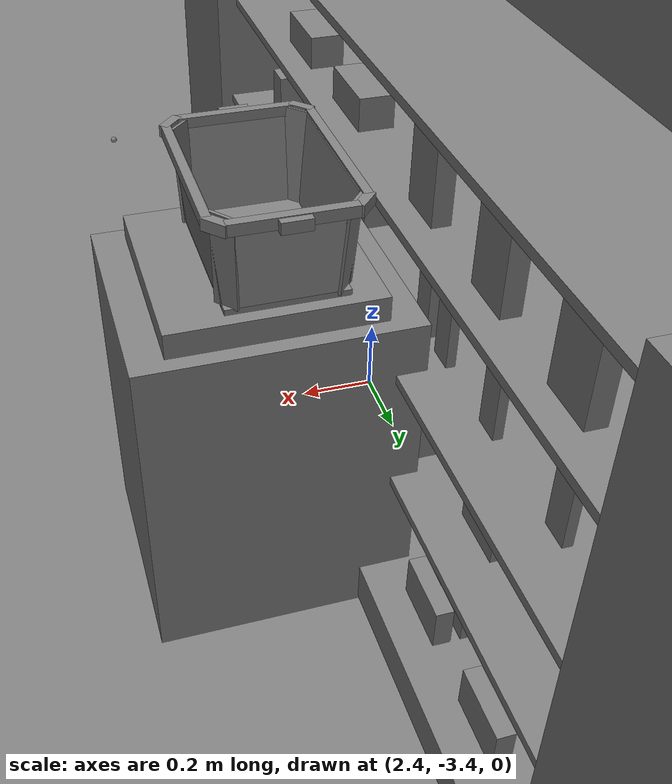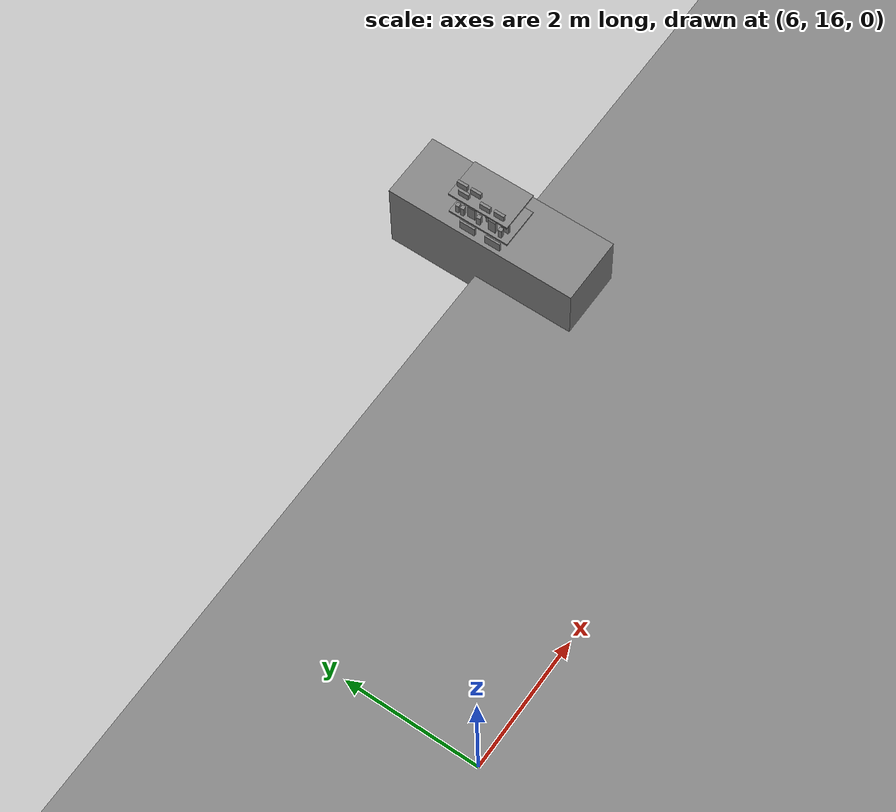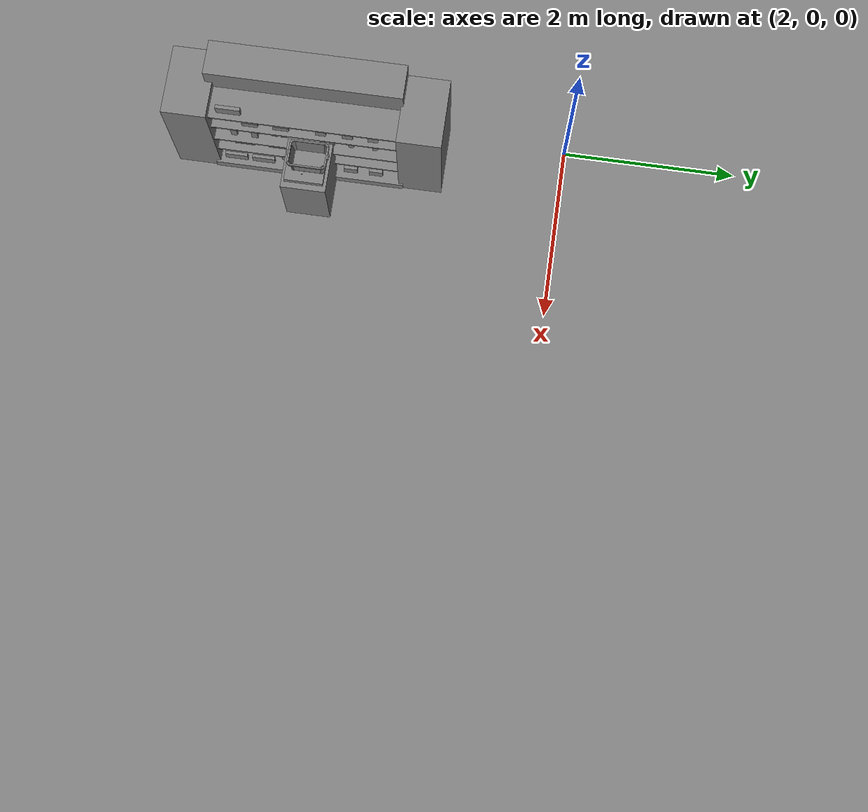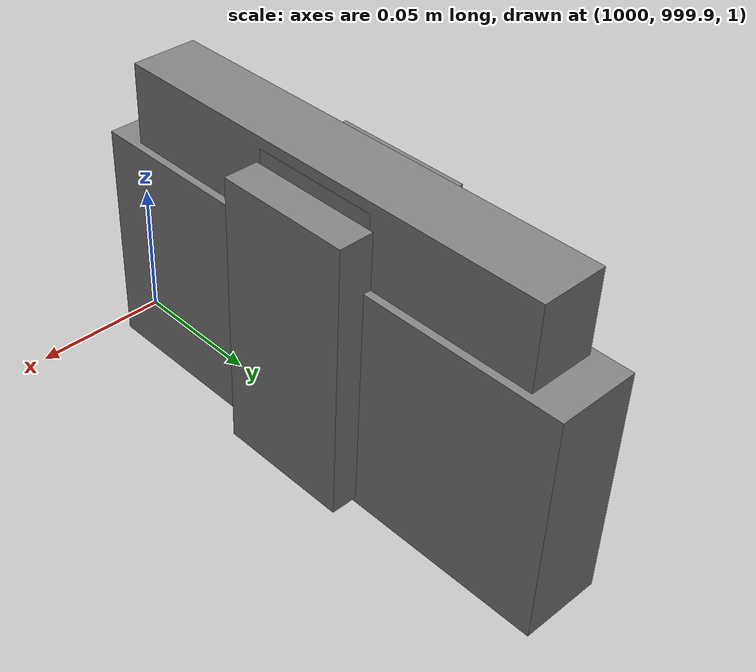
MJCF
<mujoco>
    <option gravity="0.000000000 0.000000000 -9.810000420" timestep="0.0166666" integrator="implicitfast" density="1.225" viscosity="1.8000001e-05" noslip_iterations="10" iterations="100" sdf_iterations="50">
        <flag multiccd="disable"/>
    </option>
    <size memory="1000M"/>
    <compiler coordinate="local"/>
    <worldbody>
        <light cutoff="30" pos="0 1 1" dir="0 -1 -2"/>
        <light cutoff="30" pos="0 -1 1" dir="0 1 -2"/>
        <body pos="2.497505903 -3.185120821 0.763295174" euler="0.000000000 0.000000000 0.000000000" name="openloong_gripper_2f85_fix_base_usda_jiazi_02_e_medicine_03_d">
            <geom contype="1" conaffinity="1" density="1000" type="box" material="" rgba="0.500000000 0.500000000 0.500000000 1.000000000" solimp="0.899999976 0.949999988 0.001000000" friction="1.000000000 0.005000000 0.000100000" solref="0.020000000 1.000000000" margin="0" condim="3" group="0" pos="0.000000000 0.000000000 0.000000000" quat="1.000000000 0.000000000 0.000000000 0.000000000" size="0.035000000 0.035000000 0.071999997" name="openloong_gripper_2f85_fix_base_usda_jiazi_02_e_medicine_03_d_E841CD30_3468_4B55_B504_6E8C62D1DA57"/>
            <freejoint name="openloong_gripper_2f85_fix_base_usda_jiazi_02_e_medicine_03_d"/>
        </body>
        <body pos="2.859023094 -2.828485012 0.874997377" euler="89.999946594 0.000000000 0.000000000" name="openloong_gripper_2f85_fix_base_usda_MedicineChest">
            <geom contype="1" conaffinity="1" density="100000" type="box" material="" rgba="0.500000000 0.500000000 0.500000000 1.000000000" solimp="0.899999976 0.949999988 0.001000000" friction="1.000000000 0.899999976 0.000100000" solref="0.020000000 1.000000000" margin="0" condim="3" group="0" pos="-0.132964611 0.198016286 0.194559574" quat="0.359685898 -0.000000596 -0.933073401 0.000003695" size="0.010000000 0.012000000 0.026000001" name="openloong_gripper_2f85_fix_base_usda_geom_64891B78_B7A7_49FD_92D5_F122D3461ADE"/>
            <geom contype="1" conaffinity="1" density="100000" type="box" material="" rgba="0.500000000 0.500000000 0.500000000 1.000000000" solimp="0.899999976 0.949999988 0.001000000" friction="1.000000000 0.899999976 0.000100000" solref="0.020000000 1.000000000" margin="0" condim="3" group="0" pos="0.000526667 0.104760587 -0.187798262" quat="0.705659389 -0.045368463 0.705640316 -0.045367181" size="0.003000000 0.100000001 0.100000001" name="openloong_gripper_2f85_fix_base_usda_geom_FC5526A4_8027_46AC_81E3_D1B511B7C5D4"/>
            <geom contype="1" conaffinity="1" density="100000" type="box" material="" rgba="0.500000000 0.500000000 0.500000000 1.000000000" solimp="0.899999976 0.949999988 0.001000000" friction="1.000000000 0.899999976 0.000100000" solref="0.020000000 1.000000000" margin="0" condim="3" group="0" pos="-0.000797749 0.196027160 -0.223680258" quat="0.707158327 -0.000001520 0.707055092 -0.000001520" size="0.010000000 0.012000000 0.029999999" name="openloong_gripper_2f85_fix_base_usda_geom_86EEAFFA_149F_4D58_A655_25E039F730DB"/>
            <geom contype="1" conaffinity="1" density="100000" type="box" material="" rgba="0.500000000 0.500000000 0.500000000 1.000000000" solimp="0.899999976 0.949999988 0.001000000" friction="1.000000000 0.899999976 0.000100000" solref="0.020000000 1.000000000" margin="0" condim="3" group="0" pos="0.000000000 0.005823255 0.000000000" quat="1.000000000 0.000000000 0.000000000 0.000000000" size="0.122000001 0.006000000 0.180000007" name="openloong_gripper_2f85_fix_base_usda_geom_07AF576E_E82F_4EAF_BA74_ADBED3C00C48"/>
            <geom contype="1" conaffinity="1" density="100000" type="box" material="" rgba="0.500000000 0.500000000 0.500000000 1.000000000" solimp="0.899999976 0.949999988 0.001000000" friction="1.000000000 0.899999976 0.000100000" solref="0.020000000 1.000000000" margin="0" condim="3" group="0" pos="0.000516415 0.102862239 0.189926386" quat="0.705658197 0.045368552 0.705641508 0.045367509" size="0.003000000 0.100000001 0.100000001" name="openloong_gripper_2f85_fix_base_usda_geom_1039A490_17C1_4968_9D97_31972ACCC602"/>
            <geom contype="1" conaffinity="1" density="100000" type="box" material="" rgba="0.500000000 0.500000000 0.500000000 1.000000000" solimp="0.899999976 0.949999988 0.001000000" friction="1.000000000 0.899999976 0.000100000" solref="0.020000000 1.000000000" margin="0" condim="3" group="0" pos="-0.113059282 0.107842624 0.177997828" quat="0.369108677 0.045244619 -0.928185225 -0.013556212" size="0.003000000 0.100000001 0.026000001" name="openloong_gripper_2f85_fix_base_usda_geom_49219B29_1420_4293_ADE2_DB9F6135BDD7"/>
            <geom contype="1" conaffinity="1" density="100000" type="box" material="" rgba="0.500000000 0.500000000 0.500000000 1.000000000" solimp="0.899999976 0.949999988 0.001000000" friction="1.000000000 0.899999976 0.000100000" solref="0.020000000 1.000000000" margin="0" condim="3" group="0" pos="-0.000797749 0.196027160 0.223680258" quat="0.707158327 -0.000001520 0.707055092 -0.000001520" size="0.010000000 0.012000000 0.029999999" name="openloong_gripper_2f85_fix_base_usda_geom_DAABD341_FAD4_4565_A216_5C78F7FFBEC5"/>
            <geom contype="1" conaffinity="1" density="100000" type="box" material="" rgba="0.500000000 0.500000000 0.500000000 1.000000000" solimp="0.899999976 0.949999988 0.001000000" friction="1.000000000 0.899999976 0.000100000" solref="0.020000000 1.000000000" margin="0" condim="3" group="0" pos="0.128487587 0.105749547 0.000000238" quat="0.999090791 0.000000030 -0.000000002 -0.042632505" size="0.003000000 0.100000001 0.159999996" name="openloong_gripper_2f85_fix_base_usda_geom_C1142C4B_A816_4E22_960B_CED532EFB16E"/>
            <geom contype="1" conaffinity="1" density="100000" type="box" material="" rgba="0.500000000 0.500000000 0.500000000 1.000000000" solimp="0.899999976 0.949999988 0.001000000" friction="1.000000000 0.899999976 0.000100000" solref="0.020000000 1.000000000" margin="0" condim="3" group="0" pos="-0.116801500 0.106451452 -0.175024986" quat="-0.356188178 0.039200634 -0.932773709 0.039071620" size="0.003000000 0.100000001 0.026000001" name="openloong_gripper_2f85_fix_base_usda_geom_C1B72BEC_537C_4A4A_BAFA_5C93C237D876"/>
            <geom contype="1" conaffinity="1" density="100000" type="box" material="" rgba="0.500000000 0.500000000 0.500000000 1.000000000" solimp="0.899999976 0.949999988 0.001000000" friction="1.000000000 0.899999976 0.000100000" solref="0.020000000 1.000000000" margin="0" condim="3" group="0" pos="0.000000715 0.198014379 0.208025932" quat="0.707159519 -0.000000089 0.707053959 -0.000000060" size="0.010000000 0.012000000 0.119999997" name="openloong_gripper_2f85_fix_base_usda_geom_B1D9C0D8_77C3_4D1F_9043_4CDAAD4047FC"/>
            <geom contype="1" conaffinity="1" density="100000" type="box" material="" rgba="0.500000000 0.500000000 0.500000000 1.000000000" solimp="0.899999976 0.949999988 0.001000000" friction="1.000000000 0.899999976 0.000100000" solref="0.020000000 1.000000000" margin="0" condim="3" group="0" pos="-0.133216143 0.198014021 -0.194619179" quat="-0.359760642 0.000001267 -0.933044553 0.000001341" size="0.010000000 0.012000000 0.026000001" name="openloong_gripper_2f85_fix_base_usda_geom_3A7BA3E3_54DA_446A_93AB_CDF58CD263AF"/>
            <geom contype="1" conaffinity="1" density="100000" type="box" material="" rgba="0.500000000 0.500000000 0.500000000 1.000000000" solimp="0.899999976 0.949999988 0.001000000" friction="1.000000000 0.899999976 0.000100000" solref="0.020000000 1.000000000" margin="0" condim="3" group="0" pos="0.115026236 0.107592762 0.174144983" quat="0.930772185 0.025311798 -0.363503337 -0.029796928" size="0.003000000 0.100000001 0.026000001" name="openloong_gripper_2f85_fix_base_usda_geom_0FE09A6D_8CA2_4A9A_B41E_27B60BD59075"/>
            <geom contype="1" conaffinity="1" density="100000" type="box" material="" rgba="0.500000000 0.500000000 0.500000000 1.000000000" solimp="0.899999976 0.949999988 0.001000000" friction="1.000000000 0.899999976 0.000100000" solref="0.020000000 1.000000000" margin="0" condim="3" group="0" pos="0.131582499 0.198014021 -0.194822311" quat="0.359707981 -0.000000596 -0.933064938 0.000003695" size="0.010000000 0.012000000 0.026000001" name="openloong_gripper_2f85_fix_base_usda_geom_9CA43111_5692_40B9_873C_3EBE9217A19E"/>
            <geom contype="1" conaffinity="1" density="100000" type="box" material="" rgba="0.500000000 0.500000000 0.500000000 1.000000000" solimp="0.899999976 0.949999988 0.001000000" friction="1.000000000 0.899999976 0.000100000" solref="0.020000000 1.000000000" margin="0" condim="3" group="0" pos="0.115736485 0.109648407 -0.172922373" quat="-0.356657803 0.026131347 0.933247149 -0.034088194" size="0.003000000 0.100000001 0.026000001" name="openloong_gripper_2f85_fix_base_usda_geom_BB69DA64_2684_43F0_B1F9_FF8DEFC11CBA"/>
            <geom contype="1" conaffinity="1" density="100000" type="box" material="" rgba="0.500000000 0.500000000 0.500000000 1.000000000" solimp="0.899999976 0.949999988 0.001000000" friction="1.000000000 0.899999976 0.000100000" solref="0.020000000 1.000000000" margin="0" condim="3" group="0" pos="0.145289421 0.198014736 -0.000000238" quat="1.000000000 0.000000000 0.000000000 0.000000000" size="0.009000000 0.012000000 0.180000007" name="openloong_gripper_2f85_fix_base_usda_geom_51235001_C560_4F53_9441_73C08F904F64"/>
            <geom contype="1" conaffinity="1" density="100000" type="box" material="" rgba="0.500000000 0.500000000 0.500000000 1.000000000" solimp="0.899999976 0.949999988 0.001000000" friction="1.000000000 0.899999976 0.000100000" solref="0.020000000 1.000000000" margin="0" condim="3" group="0" pos="0.000000715 0.198014379 -0.208025932" quat="0.707159519 -0.000000089 0.707053959 -0.000000060" size="0.010000000 0.012000000 0.119999997" name="openloong_gripper_2f85_fix_base_usda_geom_9B18F775_73A5_4D85_A895_04785E08B017"/>
            <geom contype="1" conaffinity="1" density="100000" type="box" material="" rgba="0.500000000 0.500000000 0.500000000 1.000000000" solimp="0.899999976 0.949999988 0.001000000" friction="1.000000000 0.899999976 0.000100000" solref="0.020000000 1.000000000" margin="0" condim="3" group="0" pos="-0.128487349 0.105749547 0.000000238" quat="0.999090791 0.000000030 -0.000000002 0.042632505" size="0.003000000 0.100000001 0.159999996" name="openloong_gripper_2f85_fix_base_usda_geom_E42DBD22_A3AB_4C41_A06E_51EED1AE530C"/>
            <geom contype="1" conaffinity="1" density="100000" type="box" material="" rgba="0.500000000 0.500000000 0.500000000 1.000000000" solimp="0.899999976 0.949999988 0.001000000" friction="1.000000000 0.899999976 0.000100000" solref="0.020000000 1.000000000" margin="0" condim="3" group="0" pos="-0.145288944 0.198014736 -0.000000238" quat="1.000000000 0.000000000 0.000000000 0.000000000" size="0.009000000 0.012000000 0.180000007" name="openloong_gripper_2f85_fix_base_usda_geom_D8715747_AA92_465D_966B_FFAB3D010481"/>
            <geom contype="1" conaffinity="1" density="100000" type="box" material="" rgba="0.500000000 0.500000000 0.500000000 1.000000000" solimp="0.899999976 0.949999988 0.001000000" friction="1.000000000 0.899999976 0.000100000" solref="0.020000000 1.000000000" margin="0" condim="3" group="0" pos="0.132833242 0.198015213 0.194798470" quat="-0.359736264 0.000001252 -0.933053970 0.000001401" size="0.010000000 0.012000000 0.026000001" name="openloong_gripper_2f85_fix_base_usda_geom_7A69B162_675D_435E_903D_9A1DB4765992"/>
            <freejoint name="openloong_gripper_2f85_fix_base_usda_MedicineChest_joint"/>
            <site size="0.005000000 0.005000000 0.005000000" rgba="0.500000000 0.500000000 0.500000000 1.000000000" pos="0.000000000 0.000000000 0.000000000" quat="1.000000000 0.000000000 0.000000000 0.000000000" group="0" type="sphere" name="openloong_gripper_2f85_fix_base_usda_MedicineChestsite"/>
        </body>
        <body pos="11.742162704 19.970987320 1.373408437" euler="0.000000000 0.000000000 -85.008651733" name="openloong_gripper_2f85_fix_base_usda_jiazi_02_e_medicine_11_pz_b">
            <geom contype="1" conaffinity="1" density="1000" type="box" material="" rgba="0.500000000 0.500000000 0.500000000 1.000000000" solimp="0.899999976 0.949999988 0.001000000" friction="1.000000000 0.005000000 0.000100000" solref="0.020000000 1.000000000" margin="0" condim="3" group="0" pos="0.000000000 0.000000000 0.000000000" quat="1.000000000 0.000000000 0.000000000 0.000000000" size="0.028000001 0.029999999 0.077000000" name="openloong_gripper_2f85_fix_base_usda_jiazi_02_e_medicine_11_pz_b_D04D4932_2D66_4B93_80D4_53063AA6ACD9"/>
            <freejoint name="openloong_gripper_2f85_fix_base_usda_jiazi_02_e_medicine_11_pz_b"/>
        </body>
        <body pos="2.540798664 -3.660816193 0.494465470" euler="0.000000000 0.000000000 0.000000000" name="openloong_gripper_2f85_fix_base_usda_jiazi_02_e_medicine_10_b">
            <geom contype="1" conaffinity="1" density="1000" type="box" material="" rgba="0.500000000 0.500000000 0.500000000 1.000000000" solimp="0.899999976 0.949999988 0.001000000" friction="1.000000000 0.005000000 0.000100000" solref="0.020000000 1.000000000" margin="0" condim="3" group="0" pos="0.000000000 0.000000000 0.000000000" quat="1.000000000 0.000000000 0.000000000 0.000000000" size="0.015000000 0.119999997 0.079000004" name="openloong_gripper_2f85_fix_base_usda_jiazi_02_e_medicine_10_b_0B55D07C_B11E_4007_89C3_491572A6FEEF"/>
            <freejoint name="openloong_gripper_2f85_fix_base_usda_jiazi_02_e_medicine_10_b"/>
        </body>
        <body pos="2.540974617 -2.142210245 0.767729700" euler="0.000000000 0.000000000 0.000000000" name="openloong_gripper_2f85_fix_base_usda_jiazi_02_e_medicine_08_d">
            <geom contype="1" conaffinity="1" density="1000" type="box" material="" rgba="0.500000000 0.500000000 0.500000000 1.000000000" solimp="0.899999976 0.949999988 0.001000000" friction="1.000000000 0.005000000 0.000100000" solref="0.020000000 1.000000000" margin="0" condim="3" group="0" pos="0.000000000 0.000000000 0.000000000" quat="1.000000000 0.000000000 0.000000000 0.000000000" size="0.010000000 0.029999999 0.075999998" name="openloong_gripper_2f85_fix_base_usda_jiazi_02_e_medicine_08_d_DD1650DC_44D9_4DD3_B167_FE690DC13043"/>
            <freejoint name="openloong_gripper_2f85_fix_base_usda_jiazi_02_e_medicine_08_d"/>
        </body>
        <body pos="2.617633820 -3.462228775 0.195964247" euler="0.000000000 0.000000000 0.000000000" name="openloong_gripper_2f85_fix_base_usda_jiazi_02_e_medicine_17_a">
            <geom contype="1" conaffinity="1" density="1000" type="box" material="" rgba="0.500000000 0.500000000 0.500000000 1.000000000" solimp="0.899999976 0.949999988 0.001000000" friction="1.000000000 0.005000000 0.000100000" solref="0.020000000 1.000000000" margin="0" condim="3" group="0" pos="0.000000000 0.000000000 0.000000000" quat="1.000000000 0.000000000 0.000000000 0.000000000" size="0.018999999 0.129999995 0.056000002" name="openloong_gripper_2f85_fix_base_usda_jiazi_02_e_medicine_17_a_8BE083C2_D791_4639_9F3C_18FC6538FCEE"/>
            <freejoint name="openloong_gripper_2f85_fix_base_usda_jiazi_02_e_medicine_17_a"/>
        </body>
        <body pos="11.835501671 19.865364075 1.405766487" euler="0.000000000 0.000000000 0.000000000" name="openloong_gripper_2f85_fix_base_usda_jiazi_02_e_medicine_11_f">
            <geom contype="1" conaffinity="1" density="1000" type="box" material="" rgba="0.500000000 0.500000000 0.500000000 1.000000000" solimp="0.899999976 0.949999988 0.001000000" friction="1.000000000 0.005000000 0.000100000" solref="0.020000000 1.000000000" margin="0" condim="3" group="0" pos="0.000000000 0.000000000 0.000000000" quat="1.000000000 0.000000000 0.000000000 0.000000000" size="0.020000000 0.057999998 0.112999998" name="openloong_gripper_2f85_fix_base_usda_jiazi_02_e_medicine_11_f_ED90B92C_A4DA_49F0_ABB8_F9EB5ADF6D47"/>
            <freejoint name="openloong_gripper_2f85_fix_base_usda_jiazi_02_e_medicine_11_f"/>
        </body>
        <body pos="2.617633820 -3.779438972 0.195964247" euler="0.000000000 0.000000000 0.000000000" name="openloong_gripper_2f85_fix_base_usda_jiazi_02_e_medicine_17_b">
            <geom contype="1" conaffinity="1" density="1000" type="box" material="" rgba="0.500000000 0.500000000 0.500000000 1.000000000" solimp="0.899999976 0.949999988 0.001000000" friction="1.000000000 0.005000000 0.000100000" solref="0.020000000 1.000000000" margin="0" condim="3" group="0" pos="0.000000000 0.000000000 0.000000000" quat="1.000000000 0.000000000 0.000000000 0.000000000" size="0.018999999 0.129999995 0.056000002" name="openloong_gripper_2f85_fix_base_usda_jiazi_02_e_medicine_17_b_84DB5AEB_8999_424A_A32C_BEFAB0CF4E31"/>
            <freejoint name="openloong_gripper_2f85_fix_base_usda_jiazi_02_e_medicine_17_b"/>
        </body>
        <body pos="11.758296013 20.215833664 1.746467471" euler="180.000000000 0.000000000 0.000000000" name="openloong_gripper_2f85_fix_base_usda_jiazi_02_e_medicine_16_e">
            <geom contype="1" conaffinity="1" density="1000" type="box" material="" rgba="0.500000000 0.500000000 0.500000000 1.000000000" solimp="0.899999976 0.949999988 0.001000000" friction="1.000000000 0.005000000 0.000100000" solref="0.020000000 1.000000000" margin="0" condim="3" group="0" pos="0.000000000 0.000000000 0.000000000" quat="0.000000000 1.000000000 0.000000000 0.000000000" size="0.020000000 0.079000004 0.052999999" name="openloong_gripper_2f85_fix_base_usda_jiazi_02_e_medicine_16_e_10FA329F_9B53_48A3_AAF7_218A24CFCF00"/>
            <freejoint name="openloong_gripper_2f85_fix_base_usda_jiazi_02_e_medicine_16_e"/>
        </body>
        <body pos="2.527985811 -2.715100288 0.458167851" euler="0.000000000 0.000000000 0.000000000" name="openloong_gripper_2f85_fix_base_usda_jiazi_02_e_medicine_13_a">
            <geom contype="1" conaffinity="1" density="1000" type="box" material="" rgba="0.500000000 0.500000000 0.500000000 1.000000000" solimp="0.899999976 0.949999988 0.001000000" friction="1.000000000 0.005000000 0.000100000" solref="0.020000000 1.000000000" margin="0" condim="3" group="0" pos="0.000000000 0.000000000 0.000000000" quat="1.000000000 0.000000000 0.000000000 0.000000000" size="0.067000002 0.068000004 0.044000000" name="openloong_gripper_2f85_fix_base_usda_jiazi_02_e_medicine_13_a_C60F2525_9805_4451_BD32_BE583030704A"/>
            <freejoint name="openloong_gripper_2f85_fix_base_usda_jiazi_02_e_medicine_13_a"/>
        </body>
        <body pos="2.557055712 -3.127499342 0.195964247" euler="0.000000000 0.000000000 0.000000000" name="openloong_gripper_2f85_fix_base_usda_jiazi_02_e_medicine_17_c">
            <geom contype="1" conaffinity="1" density="1000" type="box" material="" rgba="0.500000000 0.500000000 0.500000000 1.000000000" solimp="0.899999976 0.949999988 0.001000000" friction="1.000000000 0.005000000 0.000100000" solref="0.020000000 1.000000000" margin="0" condim="3" group="0" pos="0.000000000 0.000000000 0.000000000" quat="1.000000000 0.000000000 0.000000000 0.000000000" size="0.018999999 0.129999995 0.056000002" name="openloong_gripper_2f85_fix_base_usda_jiazi_02_e_medicine_17_c_04E3C634_D02B_4C9B_84F0_D832F3F96349"/>
            <freejoint name="openloong_gripper_2f85_fix_base_usda_jiazi_02_e_medicine_17_c"/>
        </body>
        <body pos="2.555686235 -2.149417400 1.079351544" euler="0.000000000 0.000000000 0.000000000" name="openloong_gripper_2f85_fix_base_usda_jiazi_02_e_medicine_11_b">
            <geom contype="1" conaffinity="1" density="1000" type="box" material="" rgba="0.500000000 0.500000000 0.500000000 1.000000000" solimp="0.899999976 0.949999988 0.001000000" friction="1.000000000 0.005000000 0.000100000" solref="0.020000000 1.000000000" margin="0" condim="3" group="0" pos="0.000000000 0.000000000 0.000000000" quat="1.000000000 0.000000000 0.000000000 0.000000000" size="0.020000000 0.057999998 0.112999998" name="openloong_gripper_2f85_fix_base_usda_jiazi_02_e_medicine_11_b_D2ADE7B3_69FB_4EE5_9DA3_49C0AE33BFBA"/>
            <freejoint name="openloong_gripper_2f85_fix_base_usda_jiazi_02_e_medicine_11_b"/>
        </body>
        <body pos="2.540974617 -2.413386345 0.767729700" euler="0.000000000 0.000000000 0.000000000" name="openloong_gripper_2f85_fix_base_usda_jiazi_02_e_medicine_08_c">
            <geom contype="1" conaffinity="1" density="1000" type="box" material="" rgba="0.500000000 0.500000000 0.500000000 1.000000000" solimp="0.899999976 0.949999988 0.001000000" friction="1.000000000 0.005000000 0.000100000" solref="0.020000000 1.000000000" margin="0" condim="3" group="0" pos="0.000000000 0.000000000 0.000000000" quat="1.000000000 0.000000000 0.000000000 0.000000000" size="0.010000000 0.029999999 0.075999998" name="openloong_gripper_2f85_fix_base_usda_jiazi_02_e_medicine_08_c_8AA82357_DF83_4D27_93BE_F19B616D9D82"/>
            <freejoint name="openloong_gripper_2f85_fix_base_usda_jiazi_02_e_medicine_08_c"/>
        </body>
        <body pos="2.546508551 -2.439894676 0.193254441" euler="0.000000000 0.000000000 0.000000000" name="openloong_gripper_2f85_fix_base_usda_jiazi_02_e_medicine_16_a">
            <geom contype="1" conaffinity="1" density="1000" type="box" material="" rgba="0.500000000 0.500000000 0.500000000 1.000000000" solimp="0.899999976 0.949999988 0.001000000" friction="1.000000000 0.005000000 0.000100000" solref="0.020000000 1.000000000" margin="0" condim="3" group="0" pos="0.000000000 0.000000000 0.000000000" quat="1.000000000 0.000000000 0.000000000 0.000000000" size="0.020000000 0.079000004 0.052999999" name="openloong_gripper_2f85_fix_base_usda_jiazi_02_e_medicine_16_a_3457DD9F_64EB_4891_A0B0_6112E0A98068"/>
            <freejoint name="openloong_gripper_2f85_fix_base_usda_jiazi_02_e_medicine_16_a"/>
        </body>
        <body pos="2.540974617 -2.634179592 0.767729700" euler="0.000000000 0.000000000 0.000000000" name="openloong_gripper_2f85_fix_base_usda_jiazi_02_e_medicine_08_b">
            <geom contype="1" conaffinity="1" density="1000" type="box" material="" rgba="0.500000000 0.500000000 0.500000000 1.000000000" solimp="0.899999976 0.949999988 0.001000000" friction="1.000000000 0.005000000 0.000100000" solref="0.020000000 1.000000000" margin="0" condim="3" group="0" pos="0.000000000 0.000000000 0.000000000" quat="1.000000000 0.000000000 0.000000000 0.000000000" size="0.010000000 0.029999999 0.075999998" name="openloong_gripper_2f85_fix_base_usda_jiazi_02_e_medicine_08_b_06AC2C38_3D07_42C9_890E_1D6C6B3A4ADB"/>
            <freejoint name="openloong_gripper_2f85_fix_base_usda_jiazi_02_e_medicine_08_b"/>
        </body>
        <body pos="0.000000000 0.000000000 0.000000000" euler="0.000000000 0.000000000 0.000000000" name="Static Objcets_Static Objcets">
            <geom contype="1" conaffinity="1" density="1000" type="box" material="" rgba="0.500000000 0.500000000 0.500000000 1.000000000" solimp="0.899999976 0.959999979 0.001000000" friction="1.000000000 0.005000000 0.000100000" solref="0.020000000 1.000000000" margin="0" condim="3" group="0" pos="2.433294058 -2.920555353 0.961130261" quat="1.000000000 0.000000000 0.000000000 0.000000000" size="0.200000003 1.100000024 0.010000000" name="Static Objcets_SM_jiazi_02_e_9C1201AE_DCA2_4D09_AF34_19C432A5DBC6"/>
            <geom contype="1" conaffinity="1" density="1000" type="box" material="" rgba="0.500000000 0.500000000 0.500000000 1.000000000" solimp="0.899999976 0.949999988 0.001000000" friction="1.000000000 0.005000000 0.000100000" solref="0.020000000 1.000000000" margin="0" condim="3" group="0" pos="2.064697266 -2.945113420 0.768164337" quat="1.000000000 0.000000000 0.000000000 0.000000000" size="0.200000003 1.100000024 0.750000000" name="Static Objcets_SM_jiazi_02_c_44A49197_9A5C_44DC_AB02_50C869D580F7"/>
            <geom contype="1" conaffinity="1" density="1000" type="box" material="" rgba="0.500000000 0.500000000 0.500000000 1.000000000" solimp="0.899999976 0.949999988 0.001000000" friction="1.000000000 0.005000000 0.000100000" solref="0.020000000 1.000000000" margin="0" condim="3" group="0" pos="2.285422325 -1.621193886 0.671916366" quat="1.000000000 0.000000000 0.000000000 0.000000000" size="0.400000006 0.250000000 0.649999976" name="Static Objcets_SM_jiazi_02_a_6B8C86CB_45E4_4A98_937B_4D15AEF5F47B"/>
            <geom contype="1" conaffinity="1" density="1000" type="box" material="" rgba="0.500000000 0.500000000 0.500000000 1.000000000" solimp="0.899999976 0.959999979 0.001000000" friction="1.000000000 0.005000000 0.000100000" solref="0.020000000 1.000000000" margin="0" condim="3" group="0" pos="2.506457806 -2.919259548 0.097404450" quat="1.000000000 0.000000000 0.000000000 0.000000000" size="0.200000003 1.100000024 0.050000001" name="Static Objcets_SM_jiazi_02_h_0D5D8A00_40BD_4EDB_BD91_D6B238905C23"/>
            <geom contype="1" conaffinity="1" density="1000" type="box" material="" rgba="0.500000000 0.500000000 0.500000000 1.000000000" solimp="0.899999976 0.949999988 0.001000000" friction="1.000000000 0.005000000 0.000100000" solref="0.020000000 1.000000000" margin="0" condim="3" group="0" pos="2.285422325 -4.217127323 0.670601368" quat="1.000000000 0.000000000 0.000000000 0.000000000" size="0.400000006 0.250000000 0.649999976" name="Static Objcets_SM_jiazi_02_b_5564A4A0_59B2_4C43_9AE2_054D948280A1"/>
            <geom contype="1" conaffinity="1" density="1000" type="box" material="" rgba="0.500000000 0.500000000 0.500000000 1.000000000" solimp="0.899999976 0.959999979 0.001000000" friction="1.000000000 0.005000000 0.000100000" solref="0.020000000 1.000000000" margin="0" condim="3" group="0" pos="2.452836037 -2.920555353 0.682593882" quat="1.000000000 0.000000000 0.000000000 0.000000000" size="0.200000003 1.100000024 0.010000000" name="Static Objcets_SM_jiazi_02_f_F9212432_07B6_48FB_A56B_8C28BD8F6CA4"/>
            <geom contype="1" conaffinity="1" density="1000" type="box" material="" rgba="0.500000000 0.500000000 0.500000000 1.000000000" solimp="0.899999976 0.959999979 0.001000000" friction="1.000000000 0.005000000 0.000100000" solref="0.020000000 1.000000000" margin="0" condim="3" group="0" pos="2.437276840 -2.920555353 1.214537978" quat="1.000000000 0.000000000 0.000000000 0.000000000" size="0.200000003 1.100000024 0.010000000" name="Static Objcets_SM_jiazi_02_d_BE9263EA_CE77_477D_BEA5_7379079ECD1B"/>
            <geom contype="1" conaffinity="1" density="1000" type="box" material="" rgba="0.500000000 0.500000000 0.500000000 1.000000000" solimp="0.899999976 0.959999979 0.001000000" friction="1.000000000 0.005000000 0.000100000" solref="0.020000000 1.000000000" margin="0" condim="3" group="0" pos="2.448674917 -2.920555353 0.406362146" quat="1.000000000 0.000000000 0.000000000 0.000000000" size="0.200000003 1.100000024 0.010000000" name="Static Objcets_SM_jiazi_02_g_CA3E2DDF_76EE_41A3_B6BA_E0B079634DEF"/>
            <geom contype="1" conaffinity="1" density="1000" type="box" material="" rgba="0.500000000 0.500000000 0.500000000 1.000000000" solimp="0.899999976 0.959999979 0.001000000" friction="1.000000000 0.005000000 0.000100000" solref="0.020000000 1.000000000" margin="0" condim="3" group="0" pos="11.976007462 19.950820923 1.679351807" quat="1.000000000 0.000000000 0.000000000 0.000000000" size="0.300000012 0.460000008 0.015000000" name="Static Objcets_SM_guizi_06_c_8E3938EC_1C20_40E0_97E6_A2859E70EDFC"/>
            <geom contype="1" conaffinity="1" density="1000" type="box" material="" rgba="0.500000000 0.500000000 0.500000000 1.000000000" solimp="0.899999976 0.959999979 0.001000000" friction="1.000000000 0.005000000 0.000100000" solref="0.020000000 1.000000000" margin="0" condim="3" group="0" pos="12.172613144 19.933198929 0.307627976" quat="1.000000000 0.000000000 0.000000000 0.000000000" size="0.500000000 1.450000048 0.600000024" name="Static Objcets_SM_guizi_06_a_1B79E283_4BE8_441B_9112_11C71F50FC8E"/>
            <geom contype="1" conaffinity="1" density="1000" type="plane" material="" rgba="0.500000000 0.500000000 0.500000000 1.000000000" solimp="0.899999976 0.949999988 0.001000000" friction="1.000000000 0.005000000 0.000100000" solref="0.020000000 1.000000000" margin="0" condim="3" group="0" pos="0.000000000 0.000000000 0.042896956" quat="1.000000000 0.000000000 0.000000000 0.000000000" size="20.000000000 20.000000000 1.000000000" name="Static Objcets_floor_87221256_696B_42ED_98BD_CA74CFC61BCF"/>
            <geom contype="1" conaffinity="1" density="1000" type="box" material="" rgba="0.500000000 0.500000000 0.500000000 1.000000000" solimp="0.899999976 0.959999979 0.001000000" friction="1.000000000 0.005000000 0.000100000" solref="0.020000000 1.000000000" margin="0" condim="3" group="0" pos="11.976007462 19.948400497 1.278063059" quat="1.000000000 0.000000000 0.000000000 0.000000000" size="0.300000012 0.460000008 0.015000000" name="Static Objcets_SM_guizi_06_b_FA8013B1_2979_4862_9D43_236B743DF58F"/>
        </body>
        <body pos="0.000000000 0.000000000 0.000000000" euler="0.000000000 0.000000000 0.000000000" name="Interactive Objcets_Interactive Objcets"/>
        <body pos="1000.000000000 1000.000000000 1.000000000" euler="0.000000000 0.000000000 0.000000000" name="openloong_gripper_2f85_fix_base_usda_pipalu">
            <geom contype="1" conaffinity="1" density="1000" type="box" material="" rgba="0.500000000 0.500000000 0.500000000 1.000000000" solimp="0.899999976 0.949999988 0.001000000" friction="1.000000000 0.005000000 0.000100000" solref="0.020000000 1.000000000" margin="0" condim="3" group="0" mass="0.5" pos="0.000000000 0.000000000 0.053639743" quat="1.000000000 0.000000000 0.000000000 0.000000000" size="0.011900000 0.023100000 0.053900000" name="openloong_gripper_2f85_fix_base_usda_jiazi_02_e_medicine_08_a_8C874919_55D6_4EC0_BD66_AE4B943D360D"/>
            <freejoint name="openloong_gripper_2f85_fix_base_usda_pipalu_joint"/>
            <site size="0.005000000 0.005000000 0.005000000" rgba="0.500000000 0.500000000 0.500000000 1.000000000" pos="0.000000000 0.000000000 0.000000000" quat="0.999961913 0.008726534 0.000000000 0.000000000" group="0" type="sphere" name="openloong_gripper_2f85_fix_base_usda_pipalusite"/>
        </body>
        <body pos="3.056157112 -2.458857775 1.344833255" euler="-123.920249939 12.659207344 -66.098335266" mocap="true" name="spotlight5_SpotLight"/>
        <body pos="1000.000000000 1000.000000000 1.000000000" euler="0.000000000 0.000000000 0.000000000" name="openloong_gripper_2f85_fix_base_usda_qinghuopian">
            <geom contype="1" conaffinity="1" density="1000" type="box" material="" rgba="0.500000000 0.500000000 0.500000000 1.000000000" solimp="0.899999976 0.949999988 0.001000000" friction="1.000000000 0.005000000 0.000100000" solref="0.020000000 1.000000000" margin="0" condim="3" group="0" mass="0.5" pos="0.000000000 0.000000000 0.036895368" quat="1.000000000 0.000000000 0.000000000 0.000000000" size="0.014000000 0.055300001 0.037099998" name="openloong_gripper_2f85_fix_base_usda_jiazi_02_e_medicine_16_b_6724210E_8260_4EF2_B6D6_380413A1DA6A"/>
            <freejoint name="openloong_gripper_2f85_fix_base_usda_qinghuopian_joint"/>
            <site size="0.005000000 0.005000000 0.005000000" rgba="0.500000000 0.500000000 0.500000000 1.000000000" pos="0.000000000 0.000000000 0.000000000" quat="0.999961913 0.008726534 0.000000000 0.000000000" group="0" type="sphere" name="openloong_gripper_2f85_fix_base_usda_qinghuopiansite"/>
        </body>
        <body pos="2.927494287 -2.626119375 1.314551115" euler="38.938655853 10.020511627 31.096193314" mocap="true" name="spotlight3_SpotLight"/>
        <body pos="1000.000000000 1000.000000000 1.000000000" euler="0.000000000 0.000000000 0.000000000" name="openloong_gripper_2f85_fix_base_usda_orangebox">
            <geom contype="1" conaffinity="1" density="1000" type="box" material="" rgba="0.500000000 0.500000000 0.500000000 1.000000000" solimp="0.899999976 0.949999988 0.001000000" friction="1.000000000 0.005000000 0.000100000" solref="0.020000000 1.000000000" margin="0" condim="3" group="0" mass="0.5" pos="0.000000000 0.000000000 0.051213536" quat="1.000000000 0.000000000 0.000000000 0.000000000" size="0.024499999 0.024499999 0.051099997" name="openloong_gripper_2f85_fix_base_usda_jiazi_02_e_medicine_03_a_536B2526_C42C_41E9_9F1C_A341427D0B30"/>
            <freejoint name="openloong_gripper_2f85_fix_base_usda_orangebox_joint"/>
            <site size="0.005000000 0.005000000 0.005000000" rgba="0.500000000 0.500000000 0.500000000 1.000000000" pos="0.000000000 0.000000000 0.000000000" quat="0.999961913 0.008726535 0.000000000 0.000000000" group="0" type="sphere" name="openloong_gripper_2f85_fix_base_usda_orangeboxsite"/>
        </body>
        <body pos="2.759866953 -2.527328253 1.377306461" euler="150.691696167 36.447074890 -115.694953918" mocap="true" name="spotlight1_SpotLight"/>
        <body pos="1000.000000000 1000.000000000 1.000000000" euler="0.000000000 0.000000000 0.000000000" name="openloong_gripper_2f85_fix_base_usda_niuhuangwan">
            <geom contype="1" conaffinity="1" density="1000" type="box" material="" rgba="0.500000000 0.500000000 0.500000000 1.000000000" solimp="0.899999976 0.949999988 0.001000000" friction="1.000000000 0.005000000 0.000100000" solref="0.020000000 1.000000000" margin="0" condim="3" group="0" mass="0.5" pos="0.000000000 0.000000000 0.040254507" quat="1.000000000 0.000000000 0.000000000 0.000000000" size="0.014699999 0.096599996 0.041999999" name="openloong_gripper_2f85_fix_base_usda_niuhuangwan_25DEC311_B909_4E85_93FB_D703009BE203"/>
            <freejoint name="openloong_gripper_2f85_fix_base_usda_niuhuangwan_joint"/>
            <site size="0.005000000 0.005000000 0.005000000" rgba="0.500000000 0.500000000 0.500000000 1.000000000" pos="0.000000000 0.000000000 0.000000000" quat="0.999961913 0.008726500 0.000000000 0.000000000" group="0" type="sphere" name="openloong_gripper_2f85_fix_base_usda_niuhuangwansite"/>
        </body>
        <body pos="1000.000000000 1000.000000000 1.000000000" euler="0.000000000 0.000000000 0.000000000" name="openloong_gripper_2f85_fix_base_usda_xiaokepian">
            <geom contype="1" conaffinity="1" density="1000" type="box" material="" rgba="0.500000000 0.500000000 0.500000000 1.000000000" solimp="0.899999976 0.949999988 0.001000000" friction="1.000000000 0.005000000 0.000100000" solref="0.020000000 1.000000000" margin="0" condim="3" group="0" mass="0.5" pos="0.000000000 0.000000000 0.055557761" quat="1.000000000 0.000000000 0.000000000 0.000000000" size="0.011900000 0.083999999 0.055999998" name="openloong_gripper_2f85_fix_base_usda_jiazi_02_e_medicine_10_a_A48F0663_A054_4CB0_8288_B15DB9C3BD82"/>
            <freejoint name="openloong_gripper_2f85_fix_base_usda_xiaokepian_joint"/>
            <site size="0.005000000 0.005000000 0.005000000" rgba="0.500000000 0.500000000 0.500000000 1.000000000" pos="0.000000000 0.000000000 0.000000000" quat="0.999961913 0.008726534 0.000000000 0.000000000" group="0" type="sphere" name="openloong_gripper_2f85_fix_base_usda_xiaokepiansite"/>
        </body>
        <body pos="2.877940178 -2.751950979 0.062857389" euler="0.000000000 0.000000000 0.000000000" name="[25329468500665]_DeliveryRobot_01">
            <geom contype="1" conaffinity="1" density="1000" type="box" material="" rgba="0.500000000 0.500000000 0.500000000 1.000000000" solimp="0.899999976 0.949999988 0.001000000" friction="1.000000000 0.005000000 0.000100000" solref="0.020000000 1.000000000" margin="0" condim="3" group="0" pos="0.000000000 -0.111846209 0.319800019" quat="1.000000000 0.000000000 0.000000000 0.000000000" size="0.289999992 0.254999995 0.419999987" name="[25329468500665]_geom_D936347A_DAF0_485F_A728_E6B4C0707A86"/>
            <geom contype="1" conaffinity="1" density="1000" type="box" material="" rgba="0.500000000 0.500000000 0.500000000 1.000000000" solimp="0.899999976 0.949999988 0.001000000" friction="1.000000000 0.005000000 0.000100000" solref="0.020000000 1.000000000" margin="0" condim="3" group="0" pos="0.000000000 -0.111846209 0.744405389" quat="1.000000000 0.000000000 0.000000000 0.000000000" size="0.219999999 0.219999999 0.050000001" name="[25329468500665]_geom_C51B6373_F35F_4E98_B0A5_6495904E73B6"/>
        </body>
        <body pos="2.497505903 -3.292093039 0.763295174" euler="0.000000000 0.000000000 0.000000000" name="openloong_gripper_2f85_fix_base_usda_jiazi_02_e_medicine_03_c">
            <geom contype="1" conaffinity="1" density="1000" type="box" material="" rgba="0.500000000 0.500000000 0.500000000 1.000000000" solimp="0.899999976 0.949999988 0.001000000" friction="1.000000000 0.005000000 0.000100000" solref="0.020000000 1.000000000" margin="0" condim="3" group="0" pos="0.000000000 0.000000000 0.000000000" quat="1.000000000 0.000000000 0.000000000 0.000000000" size="0.035000000 0.035000000 0.071999997" name="openloong_gripper_2f85_fix_base_usda_jiazi_02_e_medicine_03_c_9090FEF7_C191_48D7_90D6_D9CBD47478AD"/>
            <freejoint name="openloong_gripper_2f85_fix_base_usda_jiazi_02_e_medicine_03_c"/>
        </body>
        <body pos="11.763878822 20.100526810 1.405766487" euler="0.000000000 0.000000000 0.000000000" name="openloong_gripper_2f85_fix_base_usda_jiazi_02_e_medicine_11_d">
            <geom contype="1" conaffinity="1" density="1000" type="box" material="" rgba="0.500000000 0.500000000 0.500000000 1.000000000" solimp="0.899999976 0.949999988 0.001000000" friction="1.000000000 0.005000000 0.000100000" solref="0.020000000 1.000000000" margin="0" condim="3" group="0" pos="0.000000000 0.000000000 0.000000000" quat="1.000000000 0.000000000 0.000000000 0.000000000" size="0.020000000 0.057999998 0.112999998" name="openloong_gripper_2f85_fix_base_usda_jiazi_02_e_medicine_11_d_4A02AEB8_BF95_4712_9BA5_C36AA61DE278"/>
            <freejoint name="openloong_gripper_2f85_fix_base_usda_jiazi_02_e_medicine_11_d"/>
        </body>
        <body pos="11.742162704 19.632486343 1.369683743" euler="0.000000000 0.000000000 -85.008651733" name="openloong_gripper_2f85_fix_base_usda_jiazi_02_e_medicine_11_pz_a">
            <geom contype="1" conaffinity="1" density="1000" type="box" material="" rgba="0.500000000 0.500000000 0.500000000 1.000000000" solimp="0.899999976 0.949999988 0.001000000" friction="1.000000000 0.005000000 0.000100000" solref="0.020000000 1.000000000" margin="0" condim="3" group="0" pos="0.000000000 0.000000000 0.000000000" quat="1.000000000 0.000000000 0.000000000 0.000000000" size="0.028000001 0.029999999 0.077000000" name="openloong_gripper_2f85_fix_base_usda_jiazi_02_e_medicine_11_pz_a_EFCFCD7A_8F6B_4500_BDB9_54F59D3C0956"/>
            <freejoint name="openloong_gripper_2f85_fix_base_usda_jiazi_02_e_medicine_11_pz_a"/>
        </body>
        <body pos="11.835501671 19.621755600 1.405766487" euler="0.000000000 0.000000000 0.000000000" name="openloong_gripper_2f85_fix_base_usda_jiazi_02_e_medicine_11_g">
            <geom contype="1" conaffinity="1" density="1000" type="box" material="" rgba="0.500000000 0.500000000 0.500000000 1.000000000" solimp="0.899999976 0.949999988 0.001000000" friction="1.000000000 0.005000000 0.000100000" solref="0.020000000 1.000000000" margin="0" condim="3" group="0" pos="0.000000000 0.000000000 0.000000000" quat="1.000000000 0.000000000 0.000000000 0.000000000" size="0.020000000 0.057999998 0.112999998" name="openloong_gripper_2f85_fix_base_usda_jiazi_02_e_medicine_11_g_908B7B46_170E_4BE4_A929_35690A9A22D6"/>
            <freejoint name="openloong_gripper_2f85_fix_base_usda_jiazi_02_e_medicine_11_g"/>
        </body>
        <body pos="2.608781099 -2.439894676 0.193254441" euler="0.000000000 0.000000000 0.000000000" name="openloong_gripper_2f85_fix_base_usda_jiazi_02_e_medicine_16_b">
            <geom contype="1" conaffinity="1" density="1000" type="box" material="" rgba="0.500000000 0.500000000 0.500000000 1.000000000" solimp="0.899999976 0.949999988 0.001000000" friction="1.000000000 0.005000000 0.000100000" solref="0.020000000 1.000000000" margin="0" condim="3" group="0" pos="0.000000000 0.000000000 0.000000000" quat="1.000000000 0.000000000 0.000000000 0.000000000" size="0.020000000 0.079000004 0.052999999" name="openloong_gripper_2f85_fix_base_usda_jiazi_02_e_medicine_16_b_60EE5168_28F2_4AE2_9C7B_1E5EBADFD801"/>
            <freejoint name="openloong_gripper_2f85_fix_base_usda_jiazi_02_e_medicine_16_b"/>
        </body>
        <body pos="2.535823345 -3.535886526 1.006494284" euler="0.000000000 0.000000000 0.000000000" name="openloong_gripper_2f85_fix_base_usda_jiazi_02_e_medicine_01_a">
            <geom contype="1" conaffinity="1" density="1000" type="box" material="" rgba="0.500000000 0.500000000 0.500000000 1.000000000" solimp="0.899999976 0.949999988 0.001000000" friction="1.000000000 0.005000000 0.000100000" solref="0.020000000 1.000000000" margin="0" condim="3" group="0" pos="0.000000000 0.000000000 0.000000000" quat="1.000000000 0.000000000 0.000000000 0.000000000" size="0.039999999 0.090000004 0.039999999" name="openloong_gripper_2f85_fix_base_usda_jiazi_02_e_medicine_01_a_6A392E33_4B72_4C39_B2D8_67518863B7E9"/>
            <freejoint name="openloong_gripper_2f85_fix_base_usda_jiazi_02_e_medicine_01_a"/>
        </body>
        <body pos="2.535823345 -3.186250448 1.006494284" euler="0.000000000 0.000000000 0.000000000" name="openloong_gripper_2f85_fix_base_usda_jiazi_02_e_medicine_01_b">
            <geom contype="1" conaffinity="1" density="1000" type="box" material="" rgba="0.500000000 0.500000000 0.500000000 1.000000000" solimp="0.899999976 0.949999988 0.001000000" friction="1.000000000 0.005000000 0.000100000" solref="0.020000000 1.000000000" margin="0" condim="3" group="0" pos="0.000000000 0.000000000 0.000000000" quat="1.000000000 0.000000000 0.000000000 0.000000000" size="0.039999999 0.090000004 0.039999999" name="openloong_gripper_2f85_fix_base_usda_jiazi_02_e_medicine_01_b_47BBD784_AC13_4A6A_ABAD_9833AAEFA1C6"/>
            <freejoint name="openloong_gripper_2f85_fix_base_usda_jiazi_02_e_medicine_01_b"/>
        </body>
        <body pos="2.619754076 -2.721762657 0.193254441" euler="0.000000000 0.000000000 0.000000000" name="openloong_gripper_2f85_fix_base_usda_jiazi_02_e_medicine_16_d">
            <geom contype="1" conaffinity="1" density="1000" type="box" material="" rgba="0.500000000 0.500000000 0.500000000 1.000000000" solimp="0.899999976 0.949999988 0.001000000" friction="1.000000000 0.005000000 0.000100000" solref="0.020000000 1.000000000" margin="0" condim="3" group="0" pos="0.000000000 0.000000000 0.000000000" quat="1.000000000 0.000000000 0.000000000 0.000000000" size="0.020000000 0.079000004 0.052999999" name="openloong_gripper_2f85_fix_base_usda_jiazi_02_e_medicine_16_d_FF079ECA_358B_4E08_ABD1_C7F40CFAC84B"/>
            <freejoint name="openloong_gripper_2f85_fix_base_usda_jiazi_02_e_medicine_16_d"/>
        </body>
        <body pos="11.742162704 20.304208755 1.369683743" euler="0.000000000 0.000000000 -85.008651733" name="openloong_gripper_2f85_fix_base_usda_jiazi_02_e_medicine_11_pz_c">
            <geom contype="1" conaffinity="1" density="1000" type="box" material="" rgba="0.500000000 0.500000000 0.500000000 1.000000000" solimp="0.899999976 0.949999988 0.001000000" friction="1.000000000 0.005000000 0.000100000" solref="0.020000000 1.000000000" margin="0" condim="3" group="0" pos="0.000000000 0.000000000 0.000000000" quat="1.000000000 0.000000000 0.000000000 0.000000000" size="0.028000001 0.029999999 0.077000000" name="openloong_gripper_2f85_fix_base_usda_jiazi_02_e_medicine_11_pz_c_2E1DCC9B_525A_4A34_A281_3A2E2FFA30C1"/>
            <freejoint name="openloong_gripper_2f85_fix_base_usda_jiazi_02_e_medicine_11_pz_c"/>
        </body>
        <body pos="11.749706268 19.659208298 1.746467471" euler="180.000000000 0.000000000 0.000000000" name="openloong_gripper_2f85_fix_base_usda_jiazi_02_e_medicine_16_g">
            <geom contype="1" conaffinity="1" density="1000" type="box" material="" rgba="0.500000000 0.500000000 0.500000000 1.000000000" solimp="0.899999976 0.949999988 0.001000000" friction="1.000000000 0.005000000 0.000100000" solref="0.020000000 1.000000000" margin="0" condim="3" group="0" pos="0.000000000 0.000000000 0.000000000" quat="0.000000000 1.000000000 0.000000000 0.000000000" size="0.020000000 0.079000004 0.052999999" name="openloong_gripper_2f85_fix_base_usda_jiazi_02_e_medicine_16_g_8F7A7156_0954_4F85_951B_B16B2C1C57F0"/>
            <freejoint name="openloong_gripper_2f85_fix_base_usda_jiazi_02_e_medicine_16_g"/>
        </body>
        <body pos="11.742162704 20.226203918 1.369683743" euler="0.000000000 0.000000000 -85.008651733" name="openloong_gripper_2f85_fix_base_usda_jiazi_02_e_medicine_11_pz_d">
            <geom contype="1" conaffinity="1" density="1000" type="box" material="" rgba="0.500000000 0.500000000 0.500000000 1.000000000" solimp="0.899999976 0.949999988 0.001000000" friction="1.000000000 0.005000000 0.000100000" solref="0.020000000 1.000000000" margin="0" condim="3" group="0" pos="0.000000000 0.000000000 0.000000000" quat="1.000000000 0.000000000 0.000000000 0.000000000" size="0.028000001 0.029999999 0.077000000" name="openloong_gripper_2f85_fix_base_usda_jiazi_02_e_medicine_11_pz_d_E78714B1_2E6B_452D_89AF_8A36CF5B7F60"/>
            <freejoint name="openloong_gripper_2f85_fix_base_usda_jiazi_02_e_medicine_11_pz_d"/>
        </body>
        <body pos="11.751025200 19.770164490 1.405766487" euler="0.000000000 0.000000000 0.000000000" name="openloong_gripper_2f85_fix_base_usda_jiazi_02_e_medicine_11_e">
            <geom contype="1" conaffinity="1" density="1000" type="box" material="" rgba="0.500000000 0.500000000 0.500000000 1.000000000" solimp="0.899999976 0.949999988 0.001000000" friction="1.000000000 0.005000000 0.000100000" solref="0.020000000 1.000000000" margin="0" condim="3" group="0" pos="0.000000000 0.000000000 0.000000000" quat="1.000000000 0.000000000 0.000000000 0.000000000" size="0.020000000 0.057999998 0.112999998" name="openloong_gripper_2f85_fix_base_usda_jiazi_02_e_medicine_11_e_5BD61A3B_8F75_4FB7_8EA9_47CC8433AB24"/>
            <freejoint name="openloong_gripper_2f85_fix_base_usda_jiazi_02_e_medicine_11_e"/>
        </body>
        <body pos="2.608781099 -2.144529104 0.193254441" euler="0.000000000 0.000000000 0.000000000" name="openloong_gripper_2f85_fix_base_usda_jiazi_02_e_medicine_16_c">
            <geom contype="1" conaffinity="1" density="1000" type="box" material="" rgba="0.500000000 0.500000000 0.500000000 1.000000000" solimp="0.899999976 0.949999988 0.001000000" friction="1.000000000 0.005000000 0.000100000" solref="0.020000000 1.000000000" margin="0" condim="3" group="0" pos="0.000000000 0.000000000 0.000000000" quat="1.000000000 0.000000000 0.000000000 0.000000000" size="0.020000000 0.079000004 0.052999999" name="openloong_gripper_2f85_fix_base_usda_jiazi_02_e_medicine_16_c_24760554_4F3A_4910_B169_12AF745DC03E"/>
            <freejoint name="openloong_gripper_2f85_fix_base_usda_jiazi_02_e_medicine_16_c"/>
        </body>
        <body pos="11.855587959 20.093915939 1.746467471" euler="180.000000000 0.000000000 0.000000000" name="openloong_gripper_2f85_fix_base_usda_jiazi_02_e_medicine_16_i">
            <geom contype="1" conaffinity="1" density="1000" type="box" material="" rgba="0.500000000 0.500000000 0.500000000 1.000000000" solimp="0.899999976 0.949999988 0.001000000" friction="1.000000000 0.005000000 0.000100000" solref="0.020000000 1.000000000" margin="0" condim="3" group="0" pos="0.000000000 0.000000000 0.000000000" quat="0.000000000 1.000000000 0.000000000 0.000000000" size="0.020000000 0.079000004 0.052999999" name="openloong_gripper_2f85_fix_base_usda_jiazi_02_e_medicine_16_i_C1830EBE_5E9C_4600_BB81_7179A3EE9DFE"/>
            <freejoint name="openloong_gripper_2f85_fix_base_usda_jiazi_02_e_medicine_16_i"/>
        </body>
        <body pos="2.555686235 -2.437009096 1.079351544" euler="0.000000000 0.000000000 0.000000000" name="openloong_gripper_2f85_fix_base_usda_jiazi_02_e_medicine_11_a">
            <geom contype="1" conaffinity="1" density="1000" type="box" material="" rgba="0.500000000 0.500000000 0.500000000 1.000000000" solimp="0.899999976 0.949999988 0.001000000" friction="1.000000000 0.005000000 0.000100000" solref="0.020000000 1.000000000" margin="0" condim="3" group="0" pos="0.000000000 0.000000000 0.000000000" quat="1.000000000 0.000000000 0.000000000 0.000000000" size="0.020000000 0.057999998 0.112999998" name="openloong_gripper_2f85_fix_base_usda_jiazi_02_e_medicine_11_a_D91F73B7_005D_48D0_B0B0_B5FEB380CA67"/>
            <freejoint name="openloong_gripper_2f85_fix_base_usda_jiazi_02_e_medicine_11_a"/>
        </body>
        <body pos="2.543471813 -3.745966911 0.763295174" euler="0.000000000 0.000000000 0.000000000" name="openloong_gripper_2f85_fix_base_usda_jiazi_02_e_medicine_03_a">
            <geom contype="1" conaffinity="1" density="1000" type="box" material="" rgba="0.500000000 0.500000000 0.500000000 1.000000000" solimp="0.899999976 0.949999988 0.001000000" friction="1.000000000 0.005000000 0.000100000" solref="0.020000000 1.000000000" margin="0" condim="3" group="0" pos="0.000000000 0.000000000 0.000000000" quat="1.000000000 0.000000000 0.000000000 0.000000000" size="0.035000000 0.035000000 0.071999997" name="openloong_gripper_2f85_fix_base_usda_jiazi_02_e_medicine_03_a_5589433E_7D94_4EBE_88A0_40CEB1A734D1"/>
            <freejoint name="openloong_gripper_2f85_fix_base_usda_jiazi_02_e_medicine_03_a"/>
        </body>
        <body pos="2.543471813 -3.511630297 0.763295174" euler="0.000000000 0.000000000 0.000000000" name="openloong_gripper_2f85_fix_base_usda_jiazi_02_e_medicine_03_b">
            <geom contype="1" conaffinity="1" density="1000" type="box" material="" rgba="0.500000000 0.500000000 0.500000000 1.000000000" solimp="0.899999976 0.949999988 0.001000000" friction="1.000000000 0.005000000 0.000100000" solref="0.020000000 1.000000000" margin="0" condim="3" group="0" pos="0.000000000 0.000000000 0.000000000" quat="1.000000000 0.000000000 0.000000000 0.000000000" size="0.035000000 0.035000000 0.071999997" name="openloong_gripper_2f85_fix_base_usda_jiazi_02_e_medicine_03_b_7A60A582_5D58_4275_A445_8BD90F5F763F"/>
            <freejoint name="openloong_gripper_2f85_fix_base_usda_jiazi_02_e_medicine_03_b"/>
        </body>
        <body pos="2.555686235 -2.738002539 1.079351544" euler="0.000000000 0.000000000 0.000000000" name="openloong_gripper_2f85_fix_base_usda_jiazi_02_e_medicine_11_c">
            <geom contype="1" conaffinity="1" density="1000" type="box" material="" rgba="0.500000000 0.500000000 0.500000000 1.000000000" solimp="0.899999976 0.949999988 0.001000000" friction="1.000000000 0.005000000 0.000100000" solref="0.020000000 1.000000000" margin="0" condim="3" group="0" pos="0.000000000 0.000000000 0.000000000" quat="1.000000000 0.000000000 0.000000000 0.000000000" size="0.020000000 0.057999998 0.112999998" name="openloong_gripper_2f85_fix_base_usda_jiazi_02_e_medicine_11_c_D8232060_BF28_48FA_9EB5_FD9B7B07211D"/>
            <freejoint name="openloong_gripper_2f85_fix_base_usda_jiazi_02_e_medicine_11_c"/>
        </body>
        <body pos="2.540974617 -2.737313509 0.767729700" euler="0.000000000 0.000000000 0.000000000" name="openloong_gripper_2f85_fix_base_usda_jiazi_02_e_medicine_08_a">
            <geom contype="1" conaffinity="1" density="1000" type="box" material="" rgba="0.500000000 0.500000000 0.500000000 1.000000000" solimp="0.899999976 0.949999988 0.001000000" friction="1.000000000 0.005000000 0.000100000" solref="0.020000000 1.000000000" margin="0" condim="3" group="0" pos="0.000000000 0.000000000 0.000000000" quat="1.000000000 0.000000000 0.000000000 0.000000000" size="0.010000000 0.029999999 0.075999998" name="openloong_gripper_2f85_fix_base_usda_jiazi_02_e_medicine_08_a_4189B9FC_E180_4E61_B523_3A333E22B8B4"/>
            <freejoint name="openloong_gripper_2f85_fix_base_usda_jiazi_02_e_medicine_08_a"/>
        </body>
        <body pos="2.547302485 -3.744830847 1.280401945" euler="0.000000000 0.000000000 0.000000000" name="openloong_gripper_2f85_fix_base_usda_jiazi_02_e_medicine_14_b">
            <geom contype="1" conaffinity="1" density="1000" type="box" material="" rgba="0.500000000 0.500000000 0.500000000 1.000000000" solimp="0.899999976 0.949999988 0.001000000" friction="1.000000000 0.005000000 0.000100000" solref="0.020000000 1.000000000" margin="0" condim="3" group="0" pos="0.000000000 0.000000000 0.000000000" quat="1.000000000 0.000000000 0.000000000 0.000000000" size="0.021000000 0.136999995 0.057000000" name="openloong_gripper_2f85_fix_base_usda_jiazi_02_e_medicine_14_b_57880E3B_CA75_471A_A054_DA434136BA78"/>
            <freejoint name="openloong_gripper_2f85_fix_base_usda_jiazi_02_e_medicine_14_b"/>
        </body>
        <body pos="11.743835449 19.873136520 1.746467471" euler="180.000000000 0.000000000 0.000000000" name="openloong_gripper_2f85_fix_base_usda_jiazi_02_e_medicine_16_f">
            <geom contype="1" conaffinity="1" density="1000" type="box" material="" rgba="0.500000000 0.500000000 0.500000000 1.000000000" solimp="0.899999976 0.949999988 0.001000000" friction="1.000000000 0.005000000 0.000100000" solref="0.020000000 1.000000000" margin="0" condim="3" group="0" pos="0.000000000 0.000000000 0.000000000" quat="0.000000000 1.000000000 0.000000000 0.000000000" size="0.020000000 0.079000004 0.052999999" name="openloong_gripper_2f85_fix_base_usda_jiazi_02_e_medicine_16_f_2FDAD164_B014_437C_ABDB_A78F639D601F"/>
            <freejoint name="openloong_gripper_2f85_fix_base_usda_jiazi_02_e_medicine_16_f"/>
        </body>
        <body pos="11.746563911 19.764736176 0.987372577" euler="0.000000000 0.000000000 180.000000000" name="openloong_gripper_2f85_fix_base_usda_jiazi_02_e_medicine_10_d">
            <geom contype="1" conaffinity="1" density="1000" type="box" material="" rgba="0.500000000 0.500000000 0.500000000 1.000000000" solimp="0.899999976 0.949999988 0.001000000" friction="1.000000000 0.005000000 0.000100000" solref="0.020000000 1.000000000" margin="0" condim="3" group="0" pos="0.000000000 0.000000000 0.000000000" quat="0.000000000 0.000000000 0.000000000 -1.000000000" size="0.015000000 0.119999997 0.079000004" name="openloong_gripper_2f85_fix_base_usda_jiazi_02_e_medicine_10_d_650CC4C0_7EAC_42D7_8619_C17C33F62264"/>
            <freejoint name="openloong_gripper_2f85_fix_base_usda_jiazi_02_e_medicine_10_d"/>
        </body>
        <body pos="2.540798664 -3.265180588 0.494465470" euler="0.000000000 0.000000000 0.000000000" name="openloong_gripper_2f85_fix_base_usda_jiazi_02_e_medicine_10_a">
            <geom contype="1" conaffinity="1" density="1000" type="box" material="" rgba="0.500000000 0.500000000 0.500000000 1.000000000" solimp="0.899999976 0.949999988 0.001000000" friction="1.000000000 0.005000000 0.000100000" solref="0.020000000 1.000000000" margin="0" condim="3" group="0" pos="0.000000000 0.000000000 0.000000000" quat="1.000000000 0.000000000 0.000000000 0.000000000" size="0.015000000 0.119999997 0.079000004" name="openloong_gripper_2f85_fix_base_usda_jiazi_02_e_medicine_10_a_46053FB3_1D3C_4CE2_8F39_BA0F06889AC5"/>
            <freejoint name="openloong_gripper_2f85_fix_base_usda_jiazi_02_e_medicine_10_a"/>
        </body>
        <body pos="2.478220224 -2.398950338 0.458167851" euler="0.000000000 0.000000000 0.000000000" name="openloong_gripper_2f85_fix_base_usda_jiazi_02_e_medicine_13_b">
            <geom contype="1" conaffinity="1" density="1000" type="box" material="" rgba="0.500000000 0.500000000 0.500000000 1.000000000" solimp="0.899999976 0.949999988 0.001000000" friction="1.000000000 0.005000000 0.000100000" solref="0.020000000 1.000000000" margin="0" condim="3" group="0" pos="0.000000000 0.000000000 0.000000000" quat="1.000000000 0.000000000 0.000000000 0.000000000" size="0.067000002 0.068000004 0.044000000" name="openloong_gripper_2f85_fix_base_usda_jiazi_02_e_medicine_13_b_AF41A7F8_1259_4235_89A5_57CD1C95CECA"/>
            <freejoint name="openloong_gripper_2f85_fix_base_usda_jiazi_02_e_medicine_13_b"/>
        </body>
        <body pos="11.751626015 20.166509628 0.987222910" euler="0.000000000 0.000000000 0.000000000" name="openloong_gripper_2f85_fix_base_usda_jiazi_02_e_medicine_10_c">
            <geom contype="1" conaffinity="1" density="1000" type="box" material="" rgba="0.500000000 0.500000000 0.500000000 1.000000000" solimp="0.899999976 0.949999988 0.001000000" friction="1.000000000 0.005000000 0.000100000" solref="0.020000000 1.000000000" margin="0" condim="3" group="0" pos="0.000000000 0.000000000 0.000000000" quat="1.000000000 0.000000000 0.000000000 0.000000000" size="0.015000000 0.119999997 0.079000004" name="openloong_gripper_2f85_fix_base_usda_jiazi_02_e_medicine_10_c_2878DE9A_DAC5_4958_842C_72E951ADC6E3"/>
            <freejoint name="openloong_gripper_2f85_fix_base_usda_jiazi_02_e_medicine_10_c"/>
        </body>
        <body pos="11.855587959 20.303760529 1.746467471" euler="180.000000000 0.000000000 0.000000000" name="openloong_gripper_2f85_fix_base_usda_jiazi_02_e_medicine_16_h">
            <geom contype="1" conaffinity="1" density="1000" type="box" material="" rgba="0.500000000 0.500000000 0.500000000 1.000000000" solimp="0.899999976 0.949999988 0.001000000" friction="1.000000000 0.005000000 0.000100000" solref="0.020000000 1.000000000" margin="0" condim="3" group="0" pos="0.000000000 0.000000000 0.000000000" quat="0.000000000 1.000000000 0.000000000 0.000000000" size="0.020000000 0.079000004 0.052999999" name="openloong_gripper_2f85_fix_base_usda_jiazi_02_e_medicine_16_h_96A7BBDF_EFFA_4BE2_ACE7_C0156359182E"/>
            <freejoint name="openloong_gripper_2f85_fix_base_usda_jiazi_02_e_medicine_16_h"/>
        </body>
        <body pos="3.482474089 -2.842918873 0.004918467" euler="0.000000000 -17.459547043 180.000000000" mocap="true" name="openloong_gripper_2f85_fix_base_usda_leftHandMocap"/>
        <body pos="3.482474089 -2.842918873 0.004918467" euler="0.000000000 -17.459547043 180.000000000" mocap="true" name="openloong_gripper_2f85_fix_base_usda_rightHandMocap"/>
        <body pos="3.122435331 -2.842918873 1.149633169" euler="0.000000000 -17.459547043 180.000000000" name="openloong_gripper_2f85_fix_base_usda_base_link">
            <geom contype="1" conaffinity="1" density="1000" type="mesh" material="" rgba="0.783999979 0.783999979 0.783999979 1.000000000" solimp="0.899999976 0.949999988 0.001000000" friction="1.000000000 0.005000000 0.000100000" solref="0.020000000 1.000000000" margin="0" condim="3" group="3" mesh="base_link" pos="0.000000000 0.000000000 0.000000000" quat="1.000000119 0.000000000 0.000000000 0.000000000" size="1.000000000 1.000000000 1.000000000" name="openloong_gripper_2f85_fix_base_usda__geom_7_59F9A4B2_C96F_4CA7_AB96_0D4467AD0EAC"/>
            <site size="0.005000000 0.005000000 0.005000000" rgba="0.500000000 0.500000000 0.500000000 1.000000000" pos="0.000000000 0.000000000 0.000000000" quat="1.000000000 0.000000000 0.000000000 0.000000000" group="0" type="sphere" name="openloong_gripper_2f85_fix_base_usda_imu"/>
            <inertial mass="22.447001" pos="-0.005664100 -0.001336700 0.238289997" diaginertia="0.374352545 0.277180195 0.220617250" quat="0.999247074 0.035235517 -0.015086859 0.006023135"/>
            <body pos="0.000000000 0.000000000 0.299999952" euler="0.000000000 0.000000000 0.000000000" name="openloong_gripper_2f85_fix_base_usda_dummy_body">
                <geom contype="1" conaffinity="1" density="1000" type="sphere" material="" rgba="0.783999979 0.783999979 0.783999979 1.000000000" solimp="0.899999976 0.949999988 0.001000000" friction="1.000000000 0.005000000 0.000100000" solref="0.020000000 1.000000000" margin="0" condim="3" group="3" pos="0.000000000 0.000000000 0.000000000" quat="1.000000119 0.000000000 0.000000000 0.000000000" size="0.010000000 0.000000000 0.000000000" name="openloong_gripper_2f85_fix_base_usda__geom_8_EFA5270D_FCAF_42BE_BA1D_1AB921232AC8"/>
                <joint armature="0.0099999998" stiffness="0" damping="0.1" axis="0.000000 0.000000 1.000000" type="hinge" name="openloong_gripper_2f85_fix_base_usda_dummy_joint"/>
                <site size="0.010000000 0.005000000 0.005000000" rgba="0.500000000 0.500000000 0.500000000 1.000000000" pos="0.000000000 0.000000000 0.000000000" quat="1.000000000 0.000000000 0.000000000 0.000000000" group="3" type="sphere" name="openloong_gripper_2f85_fix_base_usda_dummy_site"/>
            </body>
            <body pos="0.009000063 0.000000000 0.406399846" euler="0.000000000 0.000000000 0.000000000" name="openloong_gripper_2f85_fix_base_usda_Link_head_yaw">
                <geom contype="1" conaffinity="1" density="1000" type="mesh" material="" rgba="0.783999979 0.783999979 0.783999979 1.000000000" solimp="0.899999976 0.949999988 0.001000000" friction="1.000000000 0.005000000 0.000100000" solref="0.020000000 1.000000000" margin="0" condim="3" group="3" mesh="Link_head_yaw" pos="0.000000000 0.000000000 0.000000000" quat="1.000000119 0.000000000 0.000000000 0.000000000" size="1.000000000 1.000000000 1.000000000" name="openloong_gripper_2f85_fix_base_usda__geom_10_F96EA5BA_CAEF_4AD7_AA8D_D48C16C1C65E"/>
                <inertial mass="0.84249002" pos="0.000000000 -0.002081400 0.044801001" diaginertia="0.000700588 0.000629000 0.000553812" quat="0.706933022 -0.015675601 0.015677100 0.706933022"/>
                <body pos="0.000000000 -0.034600019 0.048499823" euler="0.000000000 0.000000000 0.000000000" name="openloong_gripper_2f85_fix_base_usda_Link_head_pitch">
                    <geom contype="1" conaffinity="1" density="1000" type="mesh" material="" rgba="0.783999979 0.783999979 0.783999979 1.000000000" solimp="0.899999976 0.949999988 0.001000000" friction="1.000000000 0.005000000 0.000100000" solref="0.020000000 1.000000000" margin="0" condim="3" group="3" mesh="Link_head_pitch" pos="0.000000000 0.000000000 0.000000000" quat="1.000000119 0.000000000 0.000000000 0.000000000" size="1.000000000 1.000000000 1.000000000" name="openloong_gripper_2f85_fix_base_usda__geom_12_5E851CC7_583D_4408_B560_A0D26DCC794F"/>
                    <inertial mass="1.3943" pos="0.020569000 0.033004001 0.125000000" diaginertia="0.006381400 0.006289940 0.004481460" quat="0.973390222 0.008406822 0.228157058 0.019624906"/>
                    <body pos="0.000000000 0.029999971 0.000000000" euler="0.000000000 0.000000000 0.000000000" name="openloong_gripper_2f85_fix_base_usda_neck_center_body">
                        <site size="0.010000000 0.005000000 0.005000000" rgba="0.500000000 0.500000000 0.500000000 1.000000000" pos="0.000000000 0.000000000 0.000000000" quat="1.000000000 0.000000000 0.000000000 0.000000000" group="3" type="sphere" name="openloong_gripper_2f85_fix_base_usda_neck_center_site"/>
                        <body pos="0.019999981 0.000000000 0.149999976" euler="-0.000006687 39.998176575 -90.000205994" name="openloong_gripper_2f85_fix_base_usda_camera_head">
                            <site size="0.010000000 0.005000000 0.005000000" rgba="0.500000000 0.500000000 0.500000000 1.000000000" pos="0.000000000 0.000000000 0.000000000" quat="1.000000000 0.000000000 0.000000000 0.000000000" group="3" type="sphere" name="openloong_gripper_2f85_fix_base_usda_camera_head_site"/>
                        </body>
                    </body>
                </body>
            </body>
            <body pos="0.003999710 -0.161600113 0.392199636" euler="0.000000000 0.000000000 0.000000000" name="openloong_gripper_2f85_fix_base_usda_Link_arm_r_01">
                <geom contype="1" conaffinity="1" density="1000" type="mesh" material="" rgba="0.783999979 0.783999979 0.783999979 1.000000000" solimp="0.899999976 0.949999988 0.001000000" friction="1.000000000 0.005000000 0.000100000" solref="0.020000000 1.000000000" margin="0" condim="3" group="3" mesh="Link_arm_r_01" pos="0.000000000 0.000000000 0.000000000" quat="1.000000119 0.000000000 0.000000000 0.000000000" size="1.000000000 1.000000000 1.000000000" name="openloong_gripper_2f85_fix_base_usda__geom_14_5BB8F633_3A73_411B_A74D_509A88C848DE"/>
                <joint armature="0.0099999998" stiffness="0" damping="1" axis="0.000000 -1.000000 0.000000" limited="true" range="-170.000015259 170.000015259" type="hinge" name="openloong_gripper_2f85_fix_base_usda_J_arm_r_01"/>
                <inertial mass="0.75641" pos="0.004494600 -0.038293999 -0.000001874" diaginertia="0.000842990 0.000803050 0.000587120" quat="-0.000163502 0.707098067 0.000812463 0.707115054"/>
                <body pos="-0.041999817 -0.040999889 0.000000238" euler="0.000000000 0.000000000 0.000000000" name="openloong_gripper_2f85_fix_base_usda_Link_arm_r_02">
                    <geom contype="1" conaffinity="1" density="1000" type="mesh" material="" rgba="0.783999979 0.783999979 0.783999979 1.000000000" solimp="0.899999976 0.949999988 0.001000000" friction="1.000000000 0.005000000 0.000100000" solref="0.020000000 1.000000000" margin="0" condim="3" group="3" mesh="Link_arm_r_02" pos="0.000000000 0.000000000 0.000000000" quat="1.000000119 0.000000000 0.000000000 0.000000000" size="1.000000000 1.000000000 1.000000000" name="openloong_gripper_2f85_fix_base_usda__geom_16_19CDFD87_9C17_4DE7_AB6E_656E9C004CA4"/>
                    <joint armature="0.0099999998" stiffness="0" damping="1" axis="-1.000000 0.000000 0.000000" limited="true" range="-105.000244141 105.000244141" type="hinge" name="openloong_gripper_2f85_fix_base_usda_J_arm_r_02"/>
                    <inertial mass="0.98500001" pos="0.041999999 -0.067430697 0.000000000" diaginertia="0.002262690 0.001730990 0.001154020" quat="0.500000000 0.500000000 -0.500000000 0.500000000"/>
                    <body pos="0.041999817 -0.122600079 -0.000000238" euler="0.000000000 0.000000000 0.000000000" name="openloong_gripper_2f85_fix_base_usda_Link_arm_r_03">
                        <geom contype="1" conaffinity="1" density="1000" type="mesh" material="" rgba="0.783999979 0.783999979 0.783999979 1.000000000" solimp="0.899999976 0.949999988 0.001000000" friction="1.000000000 0.005000000 0.000100000" solref="0.020000000 1.000000000" margin="0" condim="3" group="3" mesh="Link_arm_r_03" pos="0.000000000 0.000000000 0.000000000" quat="1.000000119 0.000000000 0.000000000 0.000000000" size="1.000000000 1.000000000 1.000000000" name="openloong_gripper_2f85_fix_base_usda__geom_18_A80FFF3C_F1FF_4DBE_A6EC_6049FD572064"/>
                        <joint armature="0.0099999998" stiffness="0" damping="1" axis="0.000000 -1.000000 0.000000" limited="true" range="-170.000015259 170.000015259" type="hinge" name="openloong_gripper_2f85_fix_base_usda_J_arm_r_03"/>
                        <inertial mass="0.95899999" pos="-0.001413580 -0.164663002 0.020757901" diaginertia="0.002101340 0.002064590 0.000754802" quat="0.560480952 0.454391927 -0.443732947 0.531497955"/>
                        <body pos="0.035300255 -0.177400112 0.023999929" euler="0.000000000 0.000000000 0.000000000" name="openloong_gripper_2f85_fix_base_usda_Link_arm_r_04">
                            <geom contype="1" conaffinity="1" density="1000" type="mesh" material="" rgba="0.783999979 0.783999979 0.783999979 1.000000000" solimp="0.899999976 0.949999988 0.001000000" friction="1.000000000 0.005000000 0.000100000" solref="0.020000000 1.000000000" margin="0" condim="3" group="3" mesh="Link_arm_r_04" pos="0.000000000 0.000000000 0.000000000" quat="1.000000119 0.000000000 0.000000000 0.000000000" size="1.000000000 1.000000000 1.000000000" name="openloong_gripper_2f85_fix_base_usda__geom_20_E537E6EF_119E_4B81_840F_44A0672BD287"/>
                            <joint armature="0.0099999998" stiffness="0" damping="1" axis="-1.000000 0.000000 0.000000" limited="true" range="0.000000000 170.000015259" type="hinge" name="openloong_gripper_2f85_fix_base_usda_J_arm_r_04"/>
                            <inertial mass="0.60000002" pos="-0.038727000 -0.060766999 -0.021003000" diaginertia="0.001092610 0.000712422 0.000645102" quat="0.327701002 0.632602990 -0.467366993 0.523443997"/>
                            <body pos="-0.035300255 -0.103500128 -0.023999929" euler="0.000000000 0.000000000 0.000000000" name="openloong_gripper_2f85_fix_base_usda_Link_arm_r_05">
                                <geom contype="1" conaffinity="1" density="1000" type="mesh" material="" rgba="0.783999979 0.783999979 0.783999979 1.000000000" solimp="0.899999976 0.949999988 0.001000000" friction="1.000000000 0.005000000 0.000100000" solref="0.020000000 1.000000000" margin="0" condim="3" group="3" mesh="Link_arm_r_05" pos="0.000000000 0.000000000 0.000000000" quat="1.000000119 0.000000000 0.000000000 0.000000000" size="1.000000000 1.000000000 1.000000000" name="openloong_gripper_2f85_fix_base_usda__geom_22_A32B94CF_5242_4CA2_ABE1_261A95C19214"/>
                                <joint armature="0.0099999998" stiffness="0" damping="1" axis="0.000000 -1.000000 0.000000" limited="true" range="-170.000015259 170.000015259" type="hinge" name="openloong_gripper_2f85_fix_base_usda_J_arm_r_05"/>
                                <inertial mass="0.68976003" pos="0.000032712 -0.068658002 -0.000111780" diaginertia="0.002522510 0.002411100 0.000448695" quat="0.707660973 0.706543028 -0.002603360 0.002470550"/>
                                <body pos="-0.026499748 -0.196500063 0.000000119" euler="0.000000000 0.000000000 0.000000000" name="openloong_gripper_2f85_fix_base_usda_Link_arm_r_06">
                                    <geom contype="1" conaffinity="1" density="1000" type="mesh" material="" rgba="0.783999979 0.783999979 0.783999979 1.000000000" solimp="0.899999976 0.949999988 0.001000000" friction="1.000000000 0.005000000 0.000100000" solref="0.020000000 1.000000000" margin="0" condim="3" group="3" mesh="Link_arm_r_06" pos="0.000000000 0.000000000 0.000000000" quat="1.000000119 0.000000000 0.000000000 0.000000000" size="1.000000000 1.000000000 1.000000000" name="openloong_gripper_2f85_fix_base_usda__geom_24_78DD384A_3F22_406B_A7EE_D7DB6F0AAA49"/>
                                    <joint armature="0.0099999998" stiffness="0" damping="1" axis="1.000000 0.000000 0.000000" limited="true" range="-105.000244141 105.000244141" type="hinge" name="openloong_gripper_2f85_fix_base_usda_J_arm_r_06"/>
                                    <inertial mass="0.28" pos="0.026078001 -0.000000896 0.001663700" diaginertia="0.000156930 0.000145601 0.000104979" quat="0.707080841 0.001851080 0.001883810 0.707127810"/>
                                    <body pos="0.026500225 0.000000000 0.031800151" euler="0.000000000 0.000000000 0.000000000" name="openloong_gripper_2f85_fix_base_usda_Link_arm_r_07">
                                        <geom contype="1" conaffinity="1" density="1000" type="mesh" material="" rgba="0.783999979 0.783999979 0.783999979 1.000000000" solimp="0.899999976 0.949999988 0.001000000" friction="1.000000000 0.005000000 0.000100000" solref="0.020000000 1.000000000" margin="0" condim="3" group="3" mesh="Link_arm_r_07" pos="0.000000000 0.000000000 0.000000000" quat="1.000000119 0.000000000 0.000000000 0.000000000" size="1.000000000 1.000000000 1.000000000" name="openloong_gripper_2f85_fix_base_usda__geom_26_C5147455_4DAE_4B16_AF2F_6730E2CB94D7"/>
                                        <joint armature="0.0099999998" stiffness="0" damping="1" axis="0.000000 0.000000 1.000000" limited="true" range="-60.000133514 60.000133514" type="hinge" name="openloong_gripper_2f85_fix_base_usda_J_arm_r_07"/>
                                        <inertial mass="0.61353999" pos="-0.007859000 -0.158170000 -0.027736001" diaginertia="0.003037610 0.002570910 0.000729379" quat="0.427542925 0.443532884 -0.553093910 0.560867906"/>
                                        <body pos="-0.000000238 0.286999941 -0.270000100" euler="150.000350952 0.000001649 0.000000442" name="openloong_gripper_2f85_fix_base_usda_camera_wrist_r">
                                            <site size="0.010000000 0.005000000 0.005000000" rgba="0.500000000 0.500000000 0.500000000 1.000000000" pos="0.000000000 0.000000000 0.000000000" quat="1.000000000 0.000000000 0.000000000 0.000000000" group="3" type="sphere" name="openloong_gripper_2f85_fix_base_usda_camera_wrist_r_site"/>
                                        </body>
                                        <body pos="-0.000000477 -0.220000029 -0.033000231" euler="0.000000000 0.000000000 179.999969482" name="openloong_gripper_2f85_fix_base_usda_ee_center_body_r">
                                            <site size="0.010000000 0.005000000 0.005000000" rgba="0.500000000 0.500000000 0.500000000 1.000000000" pos="0.000000000 0.000000000 0.000000000" quat="1.000000000 0.000000000 0.000000000 0.000000000" group="3" type="sphere" name="openloong_gripper_2f85_fix_base_usda_ee_center_site_r"/>
                                        </body>
                                        <body pos="-0.000000238 -0.065999985 -0.031000376" euler="89.999992371 0.000000604 -180.000000000" name="openloong_gripper_2f85_fix_base_usda_zbr_base_link">
                                            <geom contype="1" conaffinity="1" density="1000" type="mesh" material="" rgba="0.783999979 0.783999979 0.783999979 1.000000000" solimp="0.899999976 0.949999988 0.001000000" friction="1.000000000 0.005000000 0.000100000" solref="0.020000000 1.000000000" margin="0" condim="3" group="3" mesh="base" pos="-0.000000715 0.000000060 -0.000000238" quat="1.000000000 0.000000000 0.000000000 0.000000000" size="1.000000238 1.000000238 1.000000238" name="openloong_gripper_2f85_fix_base_usda__geom_30_33BE1C3F_9757_4D09_8447_1B22502343AC"/>
                                            <inertial mass="0.77744102" pos="0.000000000 -0.000027039 0.035467502" diaginertia="0.000260285 0.000225381 0.000152708" quat="0.999998808 -0.001528488 0.000000000 0.000000000"/>
                                            <body pos="-0.030601509 0.004750074 0.065704361" euler="-89.999984741 0.000002023 -0.000000392" name="openloong_gripper_2f85_fix_base_usda_r_left_driver">
                                                <geom contype="1" conaffinity="1" density="1000" type="mesh" material="" rgba="0.783999979 0.783999979 0.783999979 1.000000000" solimp="0.899999976 0.949999988 0.001000000" friction="1.000000000 0.005000000 0.000100000" solref="0.020000000 1.000000000" margin="0" condim="3" group="3" mesh="driver" pos="0.030601270 0.054904476 -0.004699946" quat="0.707106769 0.707106590 0.000000005 0.000000007" size="1.000000238 1.000000238 1.000000238" name="openloong_gripper_2f85_fix_base_usda__geom_32_51C50896_275F_453C_829F_3746BDA35F45"/>
                                                <joint armature="0.0049999999" stiffness="0" damping="0.1" axis="0.000000 0.000000 1.000000" limited="true" range="0.000000000 51.566200256" type="hinge" name="openloong_gripper_2f85_fix_base_usda_r_left_driver_joint"/>
                                                <inertial mass="0.0089956298" pos="0.000000000 0.017754700 0.001073140" diaginertia="0.000001724 0.000001609 0.000000322" quat="0.681301236 0.732003212 0.000000000 0.000000000"/>
                                                <body pos="-0.031424768 0.004532219 -0.010199967" euler="0.000000000 0.000000000 180.000000000" name="openloong_gripper_2f85_fix_base_usda_r_left_coupler">
                                                    <geom contype="1" conaffinity="1" density="1000" type="mesh" material="" rgba="0.783999979 0.783999979 0.783999979 1.000000000" solimp="0.899999976 0.949999988 0.001000000" friction="1.000000000 0.005000000 0.000100000" solref="0.020000000 1.000000000" margin="0" condim="3" group="3" mesh="coupler" pos="-0.062025800 -0.050372254 0.005499901" quat="0.707106769 -0.707106590 -0.000000005 0.000000007" size="1.000000238 1.000000238 1.000000238" name="openloong_gripper_2f85_fix_base_usda__geom_34_31D0C3A8_ECF2_4E6C_A575_6A1C733B1FF2"/>
                                                    <inertial mass="0.0140974" pos="0.000000000 0.003012090 0.023217499" diaginertia="0.000004162 0.000003522 0.000000888" quat="0.705635548 -0.045590367 0.045590367 0.705635548"/>
                                                </body>
                                            </body>
                                            <body pos="-0.012700322 -0.012000087 0.072219744" euler="-89.999984741 0.000002023 -0.000000392" name="openloong_gripper_2f85_fix_base_usda_r_left_spring_link">
                                                <geom contype="1" conaffinity="1" density="1000" type="mesh" material="" rgba="0.783999979 0.783999979 0.783999979 1.000000000" solimp="0.899999976 0.949999988 0.001000000" friction="1.000000000 0.005000000 0.000100000" solref="0.020000000 1.000000000" margin="0" condim="3" group="3" mesh="spring_link" pos="0.012699607 0.061419979 0.012049976" quat="0.707106769 0.707106590 0.000000005 0.000000007" size="1.000000238 1.000000238 1.000000238" name="openloong_gripper_2f85_fix_base_usda__geom_36_17551CA6_C8F5_4AF5_B81D_73ECC2B37F4B"/>
                                                <joint armature="0.001" stiffness="0.050000001" damping="0.00125" axis="0.000000 0.000000 1.000000" limited="true" range="-17.000000000 51.566200256" type="hinge" name="openloong_gripper_2f85_fix_base_usda_r_left_spring_link_joint"/>
                                                <inertial mass="0.0221642" pos="-0.000000009 0.018162400 0.021265799" diaginertia="0.000008969 0.000006717 0.000002639" quat="0.663403213 -0.244737089 0.244737089 0.663403213"/>
                                                <body pos="-0.038208492 -0.042500269 0.002949954" euler="180.000000000 0.000000000 -0.002179886" name="openloong_gripper_2f85_fix_base_usda_r_left_follower">
                                                    <geom contype="1" conaffinity="1" density="1000" type="mesh" material="" rgba="0.783999979 0.783999979 0.783999979 1.000000000" solimp="0.899999976 0.949999988 0.001000000" friction="1.000000000 0.005000000 0.000100000" solref="0.020000000 1.000000000" margin="0" condim="3" group="3" mesh="follower" pos="0.050907861 -0.103920244 -0.009099962" quat="0.707106769 -0.707106709 -0.000000006 0.000000000" size="1.000000238 1.000000238 1.000000238" name="openloong_gripper_2f85_fix_base_usda__geom_39_215A478A_E7C9_48B1_AC7E_B550F00E413E"/>
                                                    <geom contype="1" conaffinity="1" density="1000" type="mesh" material="" rgba="0.783999979 0.783999979 0.783999979 1.000000000" solimp="0.899999976 0.949999988 0.001000000" friction="1.000000000 0.005000000 0.000100000" solref="0.020000000 1.000000000" margin="0" condim="3" group="3" mesh="tongue" pos="0.050907861 -0.103920244 -0.009099962" quat="0.707106769 -0.707106709 -0.000000006 0.000000000" size="1.000000238 1.000000238 1.000000238" name="openloong_gripper_2f85_fix_base_usda__geom_40_25233D78_02F7_47B6_8474_740F51B79CF0"/>
                                                    <joint armature="0.001" stiffness="0" damping="0.1" axis="0.000000 0.000000 1.000000" limited="true" range="-49.999961853 51.566200256" type="hinge" name="openloong_gripper_2f85_fix_base_usda_r_left_follower"/>
                                                    <inertial mass="0.0125222" pos="0.000000000 -0.011046000 0.012478600" diaginertia="0.000002674 0.000002456 0.000000602" quat="0.986436546 0.164143041 0.000000000 0.000000000"/>
                                                    <body pos="-0.037789591 -0.103916071 -0.009100081" euler="-89.999984741 -0.000000460 -0.000000460" name="openloong_gripper_2f85_fix_base_usda_r_left_pad">
                                                        <geom contype="1" conaffinity="1" density="1000" type="box" material="" rgba="0.449999988 0.449999988 0.449999988 1.000000000" solimp="0.949999988 0.990000010 0.001000000" friction="0.600000024 0.005000000 0.000100000" solref="0.020000000 1.000000000" margin="0" condim="3" group="3" mass="1e-06" pos="0.043258201 -0.000000060 0.138749987" quat="0.999999821 0.000000000 0.000000000 0.000000000" size="0.002000001 0.011000003 0.009375002" name="openloong_gripper_2f85_fix_base_usda_r_left_pad2_916EC0DF_CE1B_46CA_AB56_03FE13971CEB"/>
                                                        <geom contype="1" conaffinity="1" density="1000" type="box" material="" rgba="0.550000012 0.550000012 0.550000012 1.000000000" solimp="0.949999988 0.990000010 0.001000000" friction="0.699999988 0.005000000 0.000100000" solref="0.020000000 1.000000000" margin="0" condim="3" group="3" mass="1e-06" pos="0.043258201 0.000000179 0.119999796" quat="0.999999821 0.000000000 0.000000000 0.000000000" size="0.002000001 0.011000003 0.009375002" name="openloong_gripper_2f85_fix_base_usda_r_left_pad1_250CB4A6_106A_442C_B3E5_C3136E00E398"/>
                                                    </body>
                                                </body>
                                            </body>
                                            <body pos="0.030600794 -0.004749835 0.065704480" euler="89.999984741 -0.000001811 -180.000000000" name="openloong_gripper_2f85_fix_base_usda_r_right_driver">
                                                <geom contype="1" conaffinity="1" density="1000" type="mesh" material="" rgba="0.783999979 0.783999979 0.783999979 1.000000000" solimp="0.899999976 0.949999988 0.001000000" friction="1.000000000 0.005000000 0.000100000" solref="0.020000000 1.000000000" margin="0" condim="3" group="3" mesh="driver" pos="0.030601270 0.054904476 -0.004700066" quat="0.707106769 0.707106590 0.000000002 0.000000000" size="1.000000238 1.000000238 1.000000238" name="openloong_gripper_2f85_fix_base_usda__geom_42_741BC754_5D59_490F_ACC6_F77D489E6180"/>
                                                <joint armature="0.0049999999" stiffness="0" damping="0.1" axis="0.000000 0.000000 1.000000" limited="true" range="0.000000000 51.566200256" type="hinge" name="openloong_gripper_2f85_fix_base_usda_r_right_driver_joint"/>
                                                <inertial mass="0.0089956298" pos="0.000000000 0.017754700 0.001073140" diaginertia="0.000001724 0.000001609 0.000000322" quat="0.681301236 0.732003212 0.000000000 0.000000000"/>
                                                <body pos="-0.031424768 0.004532219 -0.010200026" euler="0.000000000 0.000000000 180.000000000" name="openloong_gripper_2f85_fix_base_usda_r_right_coupler">
                                                    <geom contype="1" conaffinity="1" density="1000" type="mesh" material="" rgba="0.783999979 0.783999979 0.783999979 1.000000000" solimp="0.899999976 0.949999988 0.001000000" friction="1.000000000 0.005000000 0.000100000" solref="0.020000000 1.000000000" margin="0" condim="3" group="3" mesh="coupler" pos="-0.062026277 -0.050372493 0.005499901" quat="0.707106769 -0.707106590 -0.000000002 0.000000000" size="1.000000238 1.000000238 1.000000238" name="openloong_gripper_2f85_fix_base_usda__geom_44_7CABEC4D_5147_417A_A6B0_D17ABCA014C1"/>
                                                    <inertial mass="0.0140974" pos="0.000000000 0.003012090 0.023217499" diaginertia="0.000004162 0.000003522 0.000000888" quat="0.705635548 -0.045590367 0.045590367 0.705635548"/>
                                                </body>
                                            </body>
                                            <body pos="0.012699607 0.011999908 0.072219983" euler="89.999984741 -0.000001811 -180.000000000" name="openloong_gripper_2f85_fix_base_usda_r_right_spring_link">
                                                <geom contype="1" conaffinity="1" density="1000" type="mesh" material="" rgba="0.783999979 0.783999979 0.783999979 1.000000000" solimp="0.899999976 0.949999988 0.001000000" friction="1.000000000 0.005000000 0.000100000" solref="0.020000000 1.000000000" margin="0" condim="3" group="3" mesh="spring_link" pos="0.012700084 0.061419979 0.012050155" quat="0.707106769 0.707106590 0.000000002 0.000000000" size="1.000000238 1.000000238 1.000000238" name="openloong_gripper_2f85_fix_base_usda__geom_46_04F5A8C4_98DB_4D7C_A6F5_BE57C4450360"/>
                                                <joint armature="0.001" stiffness="0.050000001" damping="0.00125" axis="0.000000 0.000000 1.000000" limited="true" range="-17.000000000 51.566200256" type="hinge" name="openloong_gripper_2f85_fix_base_usda_r_right_spring_link_joint"/>
                                                <inertial mass="0.0221642" pos="-0.000000009 0.018162400 0.021265799" diaginertia="0.000008969 0.000006717 0.000002639" quat="0.663403213 -0.244737089 0.244737089 0.663403213"/>
                                                <body pos="-0.038207777 -0.042500269 0.002949954" euler="180.000000000 0.000000000 0.000000000" name="openloong_gripper_2f85_fix_base_usda_r_right_follower">
                                                    <geom contype="1" conaffinity="1" density="1000" type="mesh" material="" rgba="0.783999979 0.783999979 0.783999979 1.000000000" solimp="0.899999976 0.949999988 0.001000000" friction="1.000000000 0.005000000 0.000100000" solref="0.020000000 1.000000000" margin="0" condim="3" group="3" mesh="follower" pos="0.050907861 -0.103920005 -0.009100081" quat="0.707106769 -0.707106590 0.000000002 0.000000000" size="1.000000238 1.000000238 1.000000238" name="openloong_gripper_2f85_fix_base_usda__geom_50_3476FDD8_05E7_49CF_BC89_20DF90ADC0FB"/>
                                                    <geom contype="1" conaffinity="1" density="1000" type="mesh" material="" rgba="0.783999979 0.783999979 0.783999979 1.000000000" solimp="0.899999976 0.949999988 0.001000000" friction="1.000000000 0.005000000 0.000100000" solref="0.020000000 1.000000000" margin="0" condim="3" group="3" mesh="tongue" pos="0.050907861 -0.103920005 -0.009100081" quat="0.707106769 -0.707106590 0.000000002 0.000000000" size="1.000000238 1.000000238 1.000000238" name="openloong_gripper_2f85_fix_base_usda__geom_49_82F5E2D1_8C0D_4111_82C5_8740A07DBEBB"/>
                                                    <joint armature="0.001" stiffness="0" damping="0.1" axis="0.000000 0.000000 1.000000" limited="true" range="-49.999961853 51.566200256" type="hinge" name="openloong_gripper_2f85_fix_base_usda_r_right_follower_joint"/>
                                                    <inertial mass="0.0125222" pos="0.000000000 -0.011046000 0.012478600" diaginertia="0.000002674 0.000002456 0.000000602" quat="0.986436546 0.164143041 0.000000000 0.000000000"/>
                                                    <body pos="-0.037789829 -0.103916071 -0.009099962" euler="-89.999961853 0.000000182 0.000000182" name="openloong_gripper_2f85_fix_base_usda_r_right_pad">
                                                        <geom contype="1" conaffinity="1" density="1000" type="box" material="" rgba="0.550000012 0.550000012 0.550000012 1.000000000" solimp="0.949999988 0.990000010 0.001000000" friction="0.699999988 0.005000000 0.000100000" solref="0.020000000 1.000000000" margin="0" condim="3" group="3" mass="1e-06" pos="0.043257963 0.000000119 0.119999915" quat="0.999999821 0.000000000 0.000000000 0.000000000" size="0.002000001 0.011000003 0.009375002" name="openloong_gripper_2f85_fix_base_usda_r_right_pad1_C6F46B16_4D10_424A_860F_F85E552ACAC7"/>
                                                        <geom contype="1" conaffinity="1" density="1000" type="box" material="" rgba="0.449999988 0.449999988 0.449999988 1.000000000" solimp="0.949999988 0.990000010 0.001000000" friction="0.600000024 0.005000000 0.000100000" solref="0.020000000 1.000000000" margin="0" condim="3" group="3" mass="1e-06" pos="0.043257963 0.000000000 0.138750106" quat="0.999999821 0.000000000 0.000000000 0.000000000" size="0.002000001 0.011000003 0.009375002" name="openloong_gripper_2f85_fix_base_usda_r_right_pad2_1AD6DCBD_24A2_46BF_81D2_BB76712A0767"/>
                                                    </body>
                                                </body>
                                            </body>
                                        </body>
                                    </body>
                                </body>
                            </body>
                        </body>
                    </body>
                </body>
            </body>
            <body pos="0.003999710 0.161600351 0.392199636" euler="0.000000000 0.000000000 0.000000000" name="openloong_gripper_2f85_fix_base_usda_Link_arm_l_01">
                <geom contype="1" conaffinity="1" density="1000" type="mesh" material="" rgba="0.783999979 0.783999979 0.783999979 1.000000000" solimp="0.899999976 0.949999988 0.001000000" friction="1.000000000 0.005000000 0.000100000" solref="0.020000000 1.000000000" margin="0" condim="3" group="3" mesh="Link_arm_l_01" pos="0.000000000 0.000000000 0.000000000" quat="1.000000119 0.000000000 0.000000000 0.000000000" size="1.000000000 1.000000000 1.000000000" name="openloong_gripper_2f85_fix_base_usda__geom_52_39F9CF8E_016D_48E4_AD16_6522B8FF4EF1"/>
                <joint armature="0.0099999998" stiffness="0" damping="1" axis="0.000000 1.000000 0.000000" limited="true" range="-170.000015259 170.000015259" type="hinge" name="openloong_gripper_2f85_fix_base_usda_J_arm_l_01"/>
                <inertial mass="0.75640601" pos="-0.004494650 0.038294200 -0.000001874" diaginertia="0.000842986 0.000803053 0.000587115" quat="-0.000812496 0.707115054 0.000163424 0.707098067"/>
                <body pos="0.042000294 0.040999889 0.000000238" euler="0.000000000 0.000000000 0.000000000" name="openloong_gripper_2f85_fix_base_usda_Link_arm_l_02">
                    <geom contype="1" conaffinity="1" density="1000" type="mesh" material="" rgba="0.783999979 0.783999979 0.783999979 1.000000000" solimp="0.899999976 0.949999988 0.001000000" friction="1.000000000 0.005000000 0.000100000" solref="0.020000000 1.000000000" margin="0" condim="3" group="3" mesh="Link_arm_l_02" pos="0.000000000 0.000000000 0.000000000" quat="1.000000119 0.000000000 0.000000000 0.000000000" size="1.000000000 1.000000000 1.000000000" name="openloong_gripper_2f85_fix_base_usda__geom_54_DDB03591_6E5A_4E46_837C_30966FEB8F67"/>
                    <joint armature="0.0099999998" stiffness="0" damping="1" axis="-1.000000 0.000000 0.000000" limited="true" range="-105.000244141 105.000244141" type="hinge" name="openloong_gripper_2f85_fix_base_usda_J_arm_l_02"/>
                    <inertial mass="0.98500001" pos="-0.041999999 0.067430697 0.000000000" diaginertia="0.002262690 0.001730990 0.001154020" quat="0.500000000 0.500000000 -0.500000000 0.500000000"/>
                    <body pos="-0.042000294 0.122600079 -0.000000238" euler="0.000000000 0.000000000 0.000000000" name="openloong_gripper_2f85_fix_base_usda_Link_arm_l_03">
                        <geom contype="1" conaffinity="1" density="1000" type="mesh" material="" rgba="0.783999979 0.783999979 0.783999979 1.000000000" solimp="0.899999976 0.949999988 0.001000000" friction="1.000000000 0.005000000 0.000100000" solref="0.020000000 1.000000000" margin="0" condim="3" group="3" mesh="Link_arm_l_03" pos="0.000000000 0.000000000 0.000000000" quat="1.000000119 0.000000000 0.000000000 0.000000000" size="1.000000000 1.000000000 1.000000000" name="openloong_gripper_2f85_fix_base_usda__geom_56_F7FBF412_3986_4E11_ADD1_E9ED5E67EA61"/>
                        <joint armature="0.0099999998" stiffness="0" damping="1" axis="0.000000 1.000000 0.000000" limited="true" range="-170.000015259 170.000015259" type="hinge" name="openloong_gripper_2f85_fix_base_usda_J_arm_l_03"/>
                        <inertial mass="0.95899999" pos="0.001413580 0.164663002 0.020757901" diaginertia="0.002101340 0.002064590 0.000754802" quat="0.443732947 0.531497955 -0.560480952 0.454391927"/>
                        <body pos="-0.035299778 0.177400112 0.023999929" euler="0.000000000 0.000000000 0.000000000" name="openloong_gripper_2f85_fix_base_usda_Link_arm_l_04">
                            <geom contype="1" conaffinity="1" density="1000" type="mesh" material="" rgba="0.783999979 0.783999979 0.783999979 1.000000000" solimp="0.899999976 0.949999988 0.001000000" friction="1.000000000 0.005000000 0.000100000" solref="0.020000000 1.000000000" margin="0" condim="3" group="3" mesh="Link_arm_l_04" pos="0.000000000 0.000000000 0.000000000" quat="1.000000119 0.000000000 0.000000000 0.000000000" size="1.000000000 1.000000000 1.000000000" name="openloong_gripper_2f85_fix_base_usda__geom_58_0319B633_31E1_4392_A36B_16A3ACDAD257"/>
                            <joint armature="0.0099999998" stiffness="0" damping="1" axis="1.000000 0.000000 0.000000" limited="true" range="0.000000000 170.000015259" type="hinge" name="openloong_gripper_2f85_fix_base_usda_J_arm_l_04"/>
                            <inertial mass="0.60000002" pos="0.038727000 0.060767200 -0.021003200" diaginertia="0.001092570 0.000712419 0.000645098" quat="0.467370987 0.523440003 -0.327692002 0.632607996"/>
                            <body pos="0.035299778 0.103500128 -0.023999929" euler="0.000000000 0.000000000 0.000000000" name="openloong_gripper_2f85_fix_base_usda_Link_arm_l_05">
                                <geom contype="1" conaffinity="1" density="1000" type="mesh" material="" rgba="0.783999979 0.783999979 0.783999979 1.000000000" solimp="0.899999976 0.949999988 0.001000000" friction="1.000000000 0.005000000 0.000100000" solref="0.020000000 1.000000000" margin="0" condim="3" group="3" mesh="Link_arm_l_05" pos="0.000000000 0.000000000 0.000000000" quat="1.000000119 0.000000000 0.000000000 0.000000000" size="1.000000000 1.000000000 1.000000000" name="openloong_gripper_2f85_fix_base_usda__geom_60_7B6D96B2_A696_4EF4_B335_90127011643C"/>
                                <joint armature="0.0099999998" stiffness="0" damping="1" axis="0.000000 1.000000 0.000000" limited="true" range="-170.000015259 170.000015259" type="hinge" name="openloong_gripper_2f85_fix_base_usda_J_arm_l_05"/>
                                <inertial mass="0.68976003" pos="-0.000032712 0.068658002 -0.000111780" diaginertia="0.002522510 0.002411100 0.000448695" quat="0.706543028 0.707660973 0.002470550 -0.002603360"/>
                                <body pos="0.026500225 0.196500063 0.000000119" euler="0.000000000 0.000000000 0.000000000" name="openloong_gripper_2f85_fix_base_usda_Link_arm_l_06">
                                    <geom contype="1" conaffinity="1" density="1000" type="mesh" material="" rgba="0.783999979 0.783999979 0.783999979 1.000000000" solimp="0.899999976 0.949999988 0.001000000" friction="1.000000000 0.005000000 0.000100000" solref="0.020000000 1.000000000" margin="0" condim="3" group="3" mesh="Link_arm_l_06" pos="0.000000000 0.000000000 0.000000000" quat="1.000000119 0.000000000 0.000000000 0.000000000" size="1.000000000 1.000000000 1.000000000" name="openloong_gripper_2f85_fix_base_usda__geom_62_E2BD2A08_2606_4A6E_A4F9_7037B4C4D1B9"/>
                                    <joint armature="0.0099999998" stiffness="0" damping="1" axis="-1.000000 0.000000 0.000000" limited="true" range="-105.000244141 105.000244141" type="hinge" name="openloong_gripper_2f85_fix_base_usda_J_arm_l_06"/>
                                    <inertial mass="0.28" pos="-0.026077701 0.000000896 0.001663730" diaginertia="0.000156927 0.000145598 0.000104981" quat="0.707080841 -0.001851280 -0.001884020 0.707127810"/>
                                    <body pos="-0.026499748 0.000000000 0.031800151" euler="0.000000000 0.000000000 0.000000000" name="openloong_gripper_2f85_fix_base_usda_Link_arm_l_07">
                                        <geom contype="1" conaffinity="1" density="1000" type="mesh" material="" rgba="0.783999979 0.783999979 0.783999979 1.000000000" solimp="0.899999976 0.949999988 0.001000000" friction="1.000000000 0.005000000 0.000100000" solref="0.020000000 1.000000000" margin="0" condim="3" group="3" mesh="Link_arm_l_07" pos="0.000000000 0.000000000 0.000000000" quat="1.000000119 0.000000000 0.000000000 0.000000000" size="1.000000000 1.000000000 1.000000000" name="openloong_gripper_2f85_fix_base_usda__geom_64_71B4C445_7206_4086_BD59_28676841BF0F"/>
                                        <joint armature="0.0099999998" stiffness="0" damping="1" axis="0.000000 0.000000 1.000000" limited="true" range="-60.000133514 60.000133514" type="hinge" name="openloong_gripper_2f85_fix_base_usda_J_arm_l_07"/>
                                        <inertial mass="0.61353999" pos="-0.007787200 0.157049999 -0.027733000" diaginertia="0.003037200 0.002570420 0.000729374" quat="0.443562120 0.427539080 -0.560871124 0.553070128"/>
                                        <body pos="-0.000000238 -0.286999941 -0.270000100" euler="-150.000350952 -0.000000799 179.976669312" name="openloong_gripper_2f85_fix_base_usda_camera_wrist_l">
                                            <site size="0.010000000 0.005000000 0.005000000" rgba="0.500000000 0.500000000 0.500000000 1.000000000" pos="0.000000000 0.000000000 0.000000000" quat="1.000000000 0.000000000 0.000000000 0.000000000" group="3" type="sphere" name="openloong_gripper_2f85_fix_base_usda_camera_wrist_l_site"/>
                                        </body>
                                        <body pos="-0.000000477 0.220000029 -0.033000231" euler="0.000000000 0.000000000 0.000000000" name="openloong_gripper_2f85_fix_base_usda_ee_center_body">
                                            <site size="0.010000000 0.005000000 0.005000000" rgba="0.500000000 0.500000000 0.500000000 1.000000000" pos="0.000000000 0.000000000 0.000000000" quat="1.000000000 0.000000000 0.000000000 0.000000000" group="3" type="sphere" name="openloong_gripper_2f85_fix_base_usda_ee_center_site"/>
                                        </body>
                                        <body pos="-0.000000238 0.065999985 -0.031000376" euler="-90.000015259 0.000000000 0.000000000" name="openloong_gripper_2f85_fix_base_usda_zbll_base_link">
                                            <geom contype="1" conaffinity="1" density="1000" type="mesh" material="" rgba="0.783999979 0.783999979 0.783999979 1.000000000" solimp="0.899999976 0.949999988 0.001000000" friction="1.000000000 0.005000000 0.000100000" solref="0.020000000 1.000000000" margin="0" condim="3" group="3" mesh="base" pos="0.000000000 0.000000000 0.000000000" quat="1.000000119 0.000000000 0.000000000 0.000000000" size="1.000000000 1.000000000 1.000000000" name="openloong_gripper_2f85_fix_base_usda__geom_68_0E8D8644_9CC2_4FD6_9B6B_C057602C7549"/>
                                            <inertial mass="0.77744102" pos="0.000000000 -0.000027039 0.035467502" diaginertia="0.000260285 0.000225381 0.000152708" quat="0.999998808 -0.001528488 0.000000000 0.000000000"/>
                                            <body pos="-0.030601263 0.004749894 0.065704107" euler="-90.000000000 -0.000000096 -0.000000096" name="openloong_gripper_2f85_fix_base_usda_l_left_driver">
                                                <geom contype="1" conaffinity="1" density="1000" type="mesh" material="" rgba="0.783999979 0.783999979 0.783999979 1.000000000" solimp="0.899999976 0.949999988 0.001000000" friction="1.000000000 0.005000000 0.000100000" solref="0.020000000 1.000000000" margin="0" condim="3" group="3" mesh="driver" pos="0.030601025 0.054904461 -0.004699886" quat="0.707106888 0.707106709 0.000000001 -0.000000007" size="1.000000000 1.000000000 1.000000000" name="openloong_gripper_2f85_fix_base_usda__geom_70_88848727_CFAE_4607_8BB0_972097BC1D5D"/>
                                                <joint armature="0.0049999999" stiffness="0" damping="0.1" axis="0.000000 0.000000 1.000000" limited="true" range="0.000000000 51.566200256" type="hinge" name="openloong_gripper_2f85_fix_base_usda_l_left_driver_joint"/>
                                                <inertial mass="0.0089956298" pos="0.000000000 0.017754700 0.001073140" diaginertia="0.000001724 0.000001609 0.000000322" quat="0.681301236 0.732003212 0.000000000 0.000000000"/>
                                                <body pos="-0.031424999 0.004532337 -0.010200143" euler="0.000000000 0.000000000 180.000000000" name="openloong_gripper_2f85_fix_base_usda_l_left_coupler">
                                                    <geom contype="1" conaffinity="1" density="1000" type="mesh" material="" rgba="0.783999979 0.783999979 0.783999979 1.000000000" solimp="0.899999976 0.949999988 0.001000000" friction="1.000000000 0.005000000 0.000100000" solref="0.020000000 1.000000000" margin="0" condim="3" group="3" mesh="coupler" pos="-0.062025785 -0.050372362 0.005500078" quat="0.707106888 -0.707106709 -0.000000001 -0.000000007" size="1.000000000 1.000000000 1.000000000" name="openloong_gripper_2f85_fix_base_usda__geom_72_A440368D_153C_411C_94C3_4A2D4CBD881C"/>
                                                    <inertial mass="0.0140974" pos="0.000000000 0.003012090 0.023217499" diaginertia="0.000004162 0.000003522 0.000000888" quat="0.705635548 -0.045590367 0.045590367 0.705635548"/>
                                                </body>
                                            </body>
                                            <body pos="-0.012700081 -0.012000680 0.072220325" euler="-90.000000000 -0.000000096 -0.000000096" name="openloong_gripper_2f85_fix_base_usda_l_left_spring_link">
                                                <geom contype="1" conaffinity="1" density="1000" type="mesh" material="" rgba="0.783999979 0.783999979 0.783999979 1.000000000" solimp="0.899999976 0.949999988 0.001000000" friction="1.000000000 0.005000000 0.000100000" solref="0.020000000 1.000000000" margin="0" condim="3" group="3" mesh="spring_link" pos="0.012699842 0.061419725 0.012049973" quat="0.707106888 0.707106709 0.000000001 -0.000000007" size="1.000000000 1.000000000 1.000000000" name="openloong_gripper_2f85_fix_base_usda__geom_74_51489C9F_9D2F_409C_9899_3776B7BE36A8"/>
                                                <joint armature="0.001" stiffness="0.050000001" damping="0.00125" axis="0.000000 0.000000 1.000000" limited="true" range="-17.000000000 51.566200256" type="hinge" name="openloong_gripper_2f85_fix_base_usda_l_left_spring_link_joint"/>
                                                <inertial mass="0.0221642" pos="-0.000000009 0.018162400 0.021265799" diaginertia="0.000008969 0.000006717 0.000002639" quat="0.663403213 -0.244737089 0.244737089 0.663403213"/>
                                                <body pos="-0.038208008 -0.042500257 0.002949953" euler="180.000000000 0.000000000 -0.002179887" name="openloong_gripper_2f85_fix_base_usda_l_left_follower">
                                                    <geom contype="1" conaffinity="1" density="1000" type="mesh" material="" rgba="0.783999979 0.783999979 0.783999979 1.000000000" solimp="0.899999976 0.949999988 0.001000000" friction="1.000000000 0.005000000 0.000100000" solref="0.020000000 1.000000000" margin="0" condim="3" group="3" mesh="follower" pos="0.050907612 -0.103919983 -0.009099960" quat="0.707106888 -0.707106829 0.000000006 0.000000000" size="1.000000000 1.000000000 1.000000000" name="openloong_gripper_2f85_fix_base_usda__geom_77_A29A0828_195C_4ECD_A559_70EF9B688997"/>
                                                    <geom contype="1" conaffinity="1" density="1000" type="mesh" material="" rgba="0.783999979 0.783999979 0.783999979 1.000000000" solimp="0.899999976 0.949999988 0.001000000" friction="1.000000000 0.005000000 0.000100000" solref="0.020000000 1.000000000" margin="0" condim="3" group="3" mesh="tongue" pos="0.050907612 -0.103919983 -0.009099960" quat="0.707106888 -0.707106829 0.000000006 0.000000000" size="1.000000000 1.000000000 1.000000000" name="openloong_gripper_2f85_fix_base_usda__geom_78_4A76B255_3F39_467B_8ABB_96635AB68DE6"/>
                                                    <joint armature="0.001" stiffness="0" damping="0.1" axis="0.000000 0.000000 1.000000" limited="true" range="-49.999961853 51.566200256" type="hinge" name="openloong_gripper_2f85_fix_base_usda_l_left_follower"/>
                                                    <inertial mass="0.0125222" pos="0.000000000 -0.011046000 0.012478600" diaginertia="0.000002674 0.000002456 0.000000602" quat="0.986436546 0.164143041 0.000000000 0.000000000"/>
                                                    <body pos="-0.037789822 -0.103915930 -0.009099841" euler="-90.000007629 0.000000452 0.000000452" name="openloong_gripper_2f85_fix_base_usda_l_left_pad">
                                                        <geom contype="1" conaffinity="1" density="1000" type="box" material="" rgba="0.550000012 0.550000012 0.550000012 1.000000000" solimp="0.949999988 0.990000010 0.001000000" friction="0.699999988 0.005000000 0.000100000" solref="0.020000000 1.000000000" margin="0" condim="3" group="3" mass="1e-06" pos="0.043258190 -0.000000238 0.120000124" quat="1.000000000 0.000000000 0.000000000 0.000000000" size="0.002000000 0.011000000 0.009375000" name="openloong_gripper_2f85_fix_base_usda_l_left_pad1_5EDA9CF4_4BA0_4990_9C3B_73D35E4DEA1D"/>
                                                        <geom contype="1" conaffinity="1" density="1000" type="box" material="" rgba="0.449999988 0.449999988 0.449999988 1.000000000" solimp="0.949999988 0.990000010 0.001000000" friction="0.600000024 0.005000000 0.000100000" solref="0.020000000 1.000000000" margin="0" condim="3" group="3" mass="1e-06" pos="0.043257713 -0.000000119 0.138749599" quat="1.000000000 0.000000000 0.000000000 0.000000000" size="0.002000000 0.011000000 0.009375000" name="openloong_gripper_2f85_fix_base_usda_l_left_pad2_5B6090E4_7E49_45FA_89D8_36F086CA115F"/>
                                                    </body>
                                                </body>
                                            </body>
                                            <body pos="0.030601025 -0.004750371 0.065704346" euler="90.000007629 0.000000000 180.000000000" name="openloong_gripper_2f85_fix_base_usda_l_right_driver">
                                                <geom contype="1" conaffinity="1" density="1000" type="mesh" material="" rgba="0.783999979 0.783999979 0.783999979 1.000000000" solimp="0.899999976 0.949999988 0.001000000" friction="1.000000000 0.005000000 0.000100000" solref="0.020000000 1.000000000" margin="0" condim="3" group="3" mesh="driver" pos="0.030601263 0.054904461 -0.004699886" quat="0.707106888 0.707106709 0.000000005 0.000000000" size="1.000000000 1.000000000 1.000000000" name="openloong_gripper_2f85_fix_base_usda__geom_80_A6F2FB58_27D6_4159_AD87_A718C79A5B51"/>
                                                <joint armature="0.0049999999" stiffness="0" damping="0.1" axis="0.000000 0.000000 1.000000" limited="true" range="0.000000000 51.566200256" type="hinge" name="openloong_gripper_2f85_fix_base_usda_l_right_driver_joint"/>
                                                <inertial mass="0.0089956298" pos="0.000000000 0.017754700 0.001073140" diaginertia="0.000001724 0.000001609 0.000000322" quat="0.681301236 0.732003212 0.000000000 0.000000000"/>
                                                <body pos="-0.031424761 0.004532337 -0.010200083" euler="0.000000000 0.000000000 180.000000000" name="openloong_gripper_2f85_fix_base_usda_l_right_coupler">
                                                    <geom contype="1" conaffinity="1" density="1000" type="mesh" material="" rgba="0.783999979 0.783999979 0.783999979 1.000000000" solimp="0.899999976 0.949999988 0.001000000" friction="1.000000000 0.005000000 0.000100000" solref="0.020000000 1.000000000" margin="0" condim="3" group="3" mesh="coupler" pos="-0.062026262 -0.050372362 0.005499721" quat="0.707106888 -0.707106709 -0.000000005 0.000000000" size="1.000000000 1.000000000 1.000000000" name="openloong_gripper_2f85_fix_base_usda__geom_82_45401A07_2B4A_4B4B_B6EC_E4A48E572E41"/>
                                                    <inertial mass="0.0140974" pos="0.000000000 0.003012090 0.023217499" diaginertia="0.000004162 0.000003522 0.000000888" quat="0.705635548 -0.045590367 0.045590367 0.705635548"/>
                                                </body>
                                            </body>
                                            <body pos="0.012699604 0.011999726 0.072220087" euler="90.000007629 0.000000000 180.000000000" name="openloong_gripper_2f85_fix_base_usda_l_right_spring_link">
                                                <geom contype="1" conaffinity="1" density="1000" type="mesh" material="" rgba="0.783999979 0.783999979 0.783999979 1.000000000" solimp="0.899999976 0.949999988 0.001000000" friction="1.000000000 0.005000000 0.000100000" solref="0.020000000 1.000000000" margin="0" condim="3" group="3" mesh="spring_link" pos="0.012700081 0.061419964 0.012050033" quat="0.707106888 0.707106709 0.000000005 0.000000000" size="1.000000000 1.000000000 1.000000000" name="openloong_gripper_2f85_fix_base_usda__geom_84_74FF596C_F6A4_4234_957B_03C275708A59"/>
                                                <joint armature="0.001" stiffness="0.050000001" damping="0.00125" axis="0.000000 0.000000 1.000000" limited="true" range="-17.000000000 51.566200256" type="hinge" name="openloong_gripper_2f85_fix_base_usda_l_right_spring_link_joint"/>
                                                <inertial mass="0.0221642" pos="-0.000000009 0.018162400 0.021265799" diaginertia="0.000008969 0.000006717 0.000002639" quat="0.663403213 -0.244737089 0.244737089 0.663403213"/>
                                                <body pos="-0.038208008 -0.042500496 0.002950013" euler="180.000000000 0.000000000 0.000000000" name="openloong_gripper_2f85_fix_base_usda_l_right_follower">
                                                    <geom contype="1" conaffinity="1" density="1000" type="mesh" material="" rgba="0.783999979 0.783999979 0.783999979 1.000000000" solimp="0.899999976 0.949999988 0.001000000" friction="1.000000000 0.005000000 0.000100000" solref="0.020000000 1.000000000" margin="0" condim="3" group="3" mesh="tongue" pos="0.050907373 -0.103919983 -0.009100139" quat="0.707106888 -0.707106709 0.000000005 -0.000000007" size="1.000000000 1.000000000 1.000000000" name="openloong_gripper_2f85_fix_base_usda__geom_87_C7F731D9_ECD5_47EB_808A_07307054F6E6"/>
                                                    <geom contype="1" conaffinity="1" density="1000" type="mesh" material="" rgba="0.783999979 0.783999979 0.783999979 1.000000000" solimp="0.899999976 0.949999988 0.001000000" friction="1.000000000 0.005000000 0.000100000" solref="0.020000000 1.000000000" margin="0" condim="3" group="3" mesh="follower" pos="0.050907373 -0.103919983 -0.009100139" quat="0.707106888 -0.707106709 0.000000005 -0.000000007" size="1.000000000 1.000000000 1.000000000" name="openloong_gripper_2f85_fix_base_usda__geom_88_19DC7868_5876_4789_9CC6_8623594410F6"/>
                                                    <joint armature="0.001" stiffness="0" damping="0.1" axis="0.000000 0.000000 1.000000" limited="true" range="-49.999961853 51.566200256" type="hinge" name="openloong_gripper_2f85_fix_base_usda_l_right_follower_joint"/>
                                                    <inertial mass="0.0125222" pos="0.000000000 -0.011046000 0.012478600" diaginertia="0.000002674 0.000002456 0.000000602" quat="0.986436546 0.164143041 0.000000000 0.000000000"/>
                                                    <body pos="-0.037789583 -0.103915930 -0.009099960" euler="-89.999992371 0.000000978 -0.000000229" name="openloong_gripper_2f85_fix_base_usda_l_right_pad">
                                                        <geom contype="1" conaffinity="1" density="1000" type="box" material="" rgba="0.449999988 0.449999988 0.449999988 1.000000000" solimp="0.949999988 0.990000010 0.001000000" friction="0.600000024 0.005000000 0.000100000" solref="0.020000000 1.000000000" margin="0" condim="3" group="3" mass="1e-06" pos="0.043257952 0.000000238 0.138750076" quat="1.000000000 0.000000000 0.000000000 0.000000000" size="0.002000000 0.011000000 0.009375000" name="openloong_gripper_2f85_fix_base_usda_l_right_pad2_97A93503_83C1_4654_B481_61D4AA8E634E"/>
                                                        <geom contype="1" conaffinity="1" density="1000" type="box" material="" rgba="0.550000012 0.550000012 0.550000012 1.000000000" solimp="0.949999988 0.990000010 0.001000000" friction="0.699999988 0.005000000 0.000100000" solref="0.020000000 1.000000000" margin="0" condim="3" group="3" mass="1e-06" pos="0.043257952 0.000000238 0.119999886" quat="1.000000000 0.000000000 0.000000000 0.000000000" size="0.002000000 0.011000000 0.009375000" name="openloong_gripper_2f85_fix_base_usda_l_right_pad1_C6A714EE_E74B_43F1_80F9_730899D651BF"/>
                                                    </body>
                                                </body>
                                            </body>
                                        </body>
                                    </body>
                                </body>
                            </body>
                        </body>
                    </body>
                </body>
            </body>
            <body pos="0.000000000 -0.065249920 0.000000000" euler="0.000000000 0.000000000 0.000000000" name="openloong_gripper_2f85_fix_base_usda_Link_waist_pitch">
                <geom contype="1" conaffinity="1" density="1000" type="mesh" material="" rgba="0.783999979 0.783999979 0.783999979 1.000000000" solimp="0.899999976 0.949999988 0.001000000" friction="1.000000000 0.005000000 0.000100000" solref="0.020000000 1.000000000" margin="0" condim="3" group="3" mesh="Link_waist_pitch" pos="0.000000000 0.000000000 0.000000000" quat="1.000000119 0.000000000 0.000000000 0.000000000" size="1.000000000 1.000000000 1.000000000" name="openloong_gripper_2f85_fix_base_usda__geom_90_1774D5CF_16D9_4CF6_898E_71CBA52D0291"/>
                <inertial mass="2.6963999" pos="-0.000734960 0.049924999 -0.000029695" diaginertia="0.006190620 0.005201250 0.004737120" quat="0.524125040 0.474713057 -0.522095084 0.476820052"/>
                <body pos="-0.064000130 0.065500021 0.000000000" euler="0.000000000 0.000000000 0.000000000" name="openloong_gripper_2f85_fix_base_usda_Link_waist_roll">
                    <geom contype="1" conaffinity="1" density="1000" type="mesh" material="" rgba="0.783999979 0.783999979 0.783999979 1.000000000" solimp="0.899999976 0.949999988 0.001000000" friction="1.000000000 0.005000000 0.000100000" solref="0.020000000 1.000000000" margin="0" condim="3" group="3" mesh="Link_waist_roll" pos="0.000000000 0.000000000 0.000000000" quat="1.000000119 0.000000000 0.000000000 0.000000000" size="1.000000000 1.000000000 1.000000000" name="openloong_gripper_2f85_fix_base_usda__geom_92_298E0730_541A_4887_9FF1_536862ECC243"/>
                    <inertial mass="2.9806001" pos="-0.003742400 -0.001000000 -0.016856000" diaginertia="0.018825000 0.017314700 0.005873970" quat="0.576995134 0.408750087 0.408750087 0.576995134"/>
                    <body pos="0.067500114 0.000000000 -0.098000169" euler="0.000000000 0.000000000 0.000000000" name="openloong_gripper_2f85_fix_base_usda_Link_waist_yaw">
                        <geom contype="1" conaffinity="1" density="1000" type="mesh" material="" rgba="0.783999979 0.783999979 0.783999979 1.000000000" solimp="0.899999976 0.949999988 0.001000000" friction="1.000000000 0.005000000 0.000100000" solref="0.020000000 1.000000000" margin="0" condim="3" group="3" mesh="Link_waist_yaw" pos="0.000000000 0.000000000 0.000000000" quat="1.000000119 0.000000000 0.000000000 0.000000000" size="1.000000000 1.000000000 1.000000000" name="openloong_gripper_2f85_fix_base_usda__geom_94_93D4F750_0FEE_40A0_9C31_04519D686EA5"/>
                        <inertial mass="7.3587999" pos="-0.096171997 -0.001000000 -0.057836000" diaginertia="0.109522998 0.089752100 0.032765999" quat="0.571972013 0.571972013 -0.415749997 0.415749997"/>
                        <body pos="-0.087500095 -0.120000124 -0.069000006" euler="0.000000000 0.000000000 0.000000000" name="openloong_gripper_2f85_fix_base_usda_Link_hip_r_roll">
                            <geom contype="1" conaffinity="1" density="1000" type="mesh" material="" rgba="0.783999979 0.783999979 0.783999979 1.000000000" solimp="0.899999976 0.949999988 0.001000000" friction="1.000000000 0.005000000 0.000100000" solref="0.020000000 1.000000000" margin="0" condim="3" group="3" mesh="Link_hip_r_roll" pos="0.000000000 0.000000000 0.000000000" quat="1.000000119 0.000000000 0.000000000 0.000000000" size="1.000000000 1.000000000 1.000000000" name="openloong_gripper_2f85_fix_base_usda__geom_96_803839B3_74ED_4D2E_95C3_79F1873F6D36"/>
                            <inertial mass="2.4333999" pos="0.075724997 -0.001061600 0.016590999" diaginertia="0.004506770 0.003996270 0.003606060" quat="0.357336968 0.610613942 0.606069922 0.363510966"/>
                            <body pos="0.082250118 -0.000999928 -0.009999871" euler="0.000000000 0.000000000 0.000000000" name="openloong_gripper_2f85_fix_base_usda_Link_hip_r_yaw">
                                <geom contype="1" conaffinity="1" density="1000" type="mesh" material="" rgba="0.783999979 0.783999979 0.783999979 1.000000000" solimp="0.899999976 0.949999988 0.001000000" friction="1.000000000 0.005000000 0.000100000" solref="0.020000000 1.000000000" margin="0" condim="3" group="3" mesh="Link_hip_r_yaw" pos="0.000000000 0.000000000 0.000000000" quat="1.000000119 0.000000000 0.000000000 0.000000000" size="1.000000000 1.000000000 1.000000000" name="openloong_gripper_2f85_fix_base_usda__geom_98_F826C3C7_EEAB_419A_B7FE_7391979E0C62"/>
                                <inertial mass="3.4303" pos="-0.000000031 -0.007135600 -0.100630000" diaginertia="0.008090100 0.007736500 0.006631600" quat="0.706536055 0.028403703 -0.028403703 0.706536055"/>
                                <body pos="0.000000000 0.036750078 -0.105500102" euler="0.000000000 0.000000000 0.000000000" name="openloong_gripper_2f85_fix_base_usda_Link_hip_r_pitch">
                                    <geom contype="1" conaffinity="1" density="1000" type="mesh" material="" rgba="0.783999979 0.783999979 0.783999979 1.000000000" solimp="0.899999976 0.949999988 0.001000000" friction="1.000000000 0.005000000 0.000100000" solref="0.020000000 1.000000000" margin="0" condim="3" group="3" mesh="Link_hip_r_pitch" pos="0.000000000 0.000000000 0.000000000" quat="1.000000119 0.000000000 0.000000000 0.000000000" size="1.000000000 1.000000000 1.000000000" name="openloong_gripper_2f85_fix_base_usda__geom_100_A8F88F53_5205_4AB0_93FF_CF206459CF1E"/>
                                    <inertial mass="5.2378001" pos="0.001085600 -0.054970000 -0.145349994" diaginertia="0.043490201 0.037812300 0.015138500" quat="0.999495864 -0.015916798 0.013696698 0.023812896"/>
                                    <body pos="0.000000000 -0.011250019 -0.399999917" euler="0.000000000 0.000000000 0.000000000" name="openloong_gripper_2f85_fix_base_usda_Link_knee_r_pitch">
                                        <geom contype="1" conaffinity="1" density="1000" type="mesh" material="" rgba="0.783999979 0.783999979 0.783999979 1.000000000" solimp="0.899999976 0.949999988 0.001000000" friction="1.000000000 0.005000000 0.000100000" solref="0.020000000 1.000000000" margin="0" condim="3" group="3" mesh="Link_knee_r_pitch" pos="0.000000000 0.000000000 0.000000000" quat="1.000000119 0.000000000 0.000000000 0.000000000" size="1.000000000 1.000000000 1.000000000" name="openloong_gripper_2f85_fix_base_usda__geom_102_3E83BE7D_2764_4F0D_A701_7350590F9DAD"/>
                                        <inertial mass="2.9775" pos="-0.009642500 0.000002934 -0.136010006" diaginertia="0.024215899 0.023851801 0.002284610" quat="0.782037616 -0.003061678 0.016178992 0.623013675"/>
                                        <body pos="0.000000000 0.000000000 -0.387000024" euler="0.000000000 0.000000000 0.000000000" name="openloong_gripper_2f85_fix_base_usda_Link_ankle_r_pitch">
                                            <geom contype="1" conaffinity="1" density="1000" type="mesh" material="" rgba="0.783999979 0.783999979 0.783999979 1.000000000" solimp="0.899999976 0.949999988 0.001000000" friction="1.000000000 0.005000000 0.000100000" solref="0.020000000 1.000000000" margin="0" condim="3" group="3" mesh="Link_ankle_r_pitch" pos="0.000000000 0.000000000 0.000000000" quat="1.000000119 0.000000000 0.000000000 0.000000000" size="1.000000000 1.000000000 1.000000000" name="openloong_gripper_2f85_fix_base_usda__geom_104_92B422FD_4A93_4EB5_8454_68E57EDB8220"/>
                                            <inertial mass="0.10145" pos="-0.000000000 -0.000000127 -0.000000025" diaginertia="0.000027175 0.000026565 0.000006112" quat="0.707106829 0.707106829 0.000000000 0.000000000"/>
                                            <body pos="0.000000000 0.000000000 0.000000000" euler="0.000000000 0.000000000 0.000000000" name="openloong_gripper_2f85_fix_base_usda_Link_ankle_r_roll">
                                                <geom contype="1" conaffinity="1" density="1000" type="box" material="" rgba="1.000000000 0.000000000 0.000000000 0.000000000" solimp="0.899999976 0.949999988 0.001000000" friction="1.000000000 0.005000000 0.000100000" solref="0.020000000 1.000000000" margin="0" condim="3" group="3" pos="0.047504663 0.000082731 -0.026545227" quat="1.000000119 0.000000000 0.000000000 0.000000000" size="0.122500002 0.039999999 0.043499999" name="openloong_gripper_2f85_fix_base_usda__geom_106_18004B05_541D_4502_BD6C_E8ACFB927686"/>
                                                <site size="0.123000003 0.041000001 0.044000000" rgba="0.000000000 1.000000000 0.000000000 0.000000000" pos="0.047504615 0.000082667 -0.026545310" quat="1.000000000 0.000000000 0.000000000 0.000000000" group="3" type="box" name="openloong_gripper_2f85_fix_base_usda_rf-tc"/>
                                                <inertial mass="0.75229001" pos="0.041078001 -0.000000089 -0.043908998" diaginertia="0.003659370 0.003646500 0.000416828" quat="0.000000000 0.677034914 0.000000000 0.735950947"/>
                                            </body>
                                        </body>
                                    </body>
                                </body>
                            </body>
                        </body>
                        <body pos="-0.087500095 0.120000124 -0.069000006" euler="0.000000000 0.000000000 0.000000000" name="openloong_gripper_2f85_fix_base_usda_Link_hip_l_roll">
                            <geom contype="1" conaffinity="1" density="1000" type="mesh" material="" rgba="0.783999979 0.783999979 0.783999979 1.000000000" solimp="0.899999976 0.949999988 0.001000000" friction="1.000000000 0.005000000 0.000100000" solref="0.020000000 1.000000000" margin="0" condim="3" group="3" mesh="Link_hip_l_roll" pos="0.000000000 0.000000000 0.000000000" quat="1.000000119 0.000000000 0.000000000 0.000000000" size="1.000000000 1.000000000 1.000000000" name="openloong_gripper_2f85_fix_base_usda__geom_108_E6477ED7_D7C9_4003_92B5_45930AE5186A"/>
                            <inertial mass="2.4333999" pos="0.075724997 -0.000938430 0.016590999" diaginertia="0.004257030 0.003974770 0.003377790" quat="0.411751240 0.573205352 0.583885372 0.401216239"/>
                            <body pos="0.082250118 -0.000999928 -0.009999871" euler="0.000000000 0.000000000 0.000000000" name="openloong_gripper_2f85_fix_base_usda_Link_hip_l_yaw">
                                <geom contype="1" conaffinity="1" density="1000" type="mesh" material="" rgba="0.783999979 0.783999979 0.783999979 1.000000000" solimp="0.899999976 0.949999988 0.001000000" friction="1.000000000 0.005000000 0.000100000" solref="0.020000000 1.000000000" margin="0" condim="3" group="3" mesh="Link_hip_l_yaw" pos="0.000000000 0.000000000 0.000000000" quat="1.000000119 0.000000000 0.000000000 0.000000000" size="1.000000000 1.000000000 1.000000000" name="openloong_gripper_2f85_fix_base_usda__geom_110_EBF4FE18_70D0_485C_AA01_88A275A93151"/>
                                <inertial mass="3.4303999" pos="-0.000000032 0.007135800 -0.100630000" diaginertia="0.008090100 0.007736500 0.006631500" quat="0.706536174 -0.028401807 0.028401807 0.706536174"/>
                                <body pos="0.000000000 -0.036750078 -0.105500102" euler="0.000000000 0.000000000 0.000000000" name="openloong_gripper_2f85_fix_base_usda_Link_hip_l_pitch">
                                    <geom contype="1" conaffinity="1" density="1000" type="mesh" material="" rgba="0.783999979 0.783999979 0.783999979 1.000000000" solimp="0.899999976 0.949999988 0.001000000" friction="1.000000000 0.005000000 0.000100000" solref="0.020000000 1.000000000" margin="0" condim="3" group="3" mesh="Link_hip_l_pitch" pos="0.000000000 0.000000000 0.000000000" quat="1.000000119 0.000000000 0.000000000 0.000000000" size="1.000000000 1.000000000 1.000000000" name="openloong_gripper_2f85_fix_base_usda__geom_112_396C6EDE_0035_41A0_937A_7FF1447BC3B4"/>
                                    <inertial mass="5.2378001" pos="0.001085600 0.054970000 -0.145349994" diaginertia="0.043490201 0.037812300 0.015138500" quat="0.999495745 0.015916597 0.013696796 -0.023821594"/>
                                    <body pos="0.000000000 0.011250019 -0.399999917" euler="0.000000000 0.000000000 0.000000000" name="openloong_gripper_2f85_fix_base_usda_Link_knee_l_pitch">
                                        <geom contype="1" conaffinity="1" density="1000" type="mesh" material="" rgba="0.783999979 0.783999979 0.783999979 1.000000000" solimp="0.899999976 0.949999988 0.001000000" friction="1.000000000 0.005000000 0.000100000" solref="0.020000000 1.000000000" margin="0" condim="3" group="3" mesh="Link_knee_l_pitch" pos="0.000000000 0.000000000 0.000000000" quat="1.000000119 0.000000000 0.000000000 0.000000000" size="1.000000000 1.000000000 1.000000000" name="openloong_gripper_2f85_fix_base_usda__geom_114_AB284A98_63C8_450E_9252_6AD30AEFB928"/>
                                        <inertial mass="2.9775" pos="-0.009642500 -0.000002868 -0.136010006" diaginertia="0.024214899 0.023850800 0.002284610" quat="0.623014212 0.016178306 -0.003060011 0.782037318"/>
                                        <body pos="0.000000000 0.000000000 -0.387000024" euler="0.000000000 0.000000000 0.000000000" name="openloong_gripper_2f85_fix_base_usda_Link_ankle_l_pitch">
                                            <geom contype="1" conaffinity="1" density="1000" type="mesh" material="" rgba="0.783999979 0.783999979 0.783999979 1.000000000" solimp="0.899999976 0.949999988 0.001000000" friction="1.000000000 0.005000000 0.000100000" solref="0.020000000 1.000000000" margin="0" condim="3" group="3" mesh="Link_ankle_l_pitch" pos="0.000000000 0.000000000 0.000000000" quat="1.000000119 0.000000000 0.000000000 0.000000000" size="1.000000000 1.000000000 1.000000000" name="openloong_gripper_2f85_fix_base_usda__geom_116_0F4419E5_D168_4107_839B_32F75BE042D2"/>
                                            <inertial mass="0.10145" pos="-0.000000000 0.000000127 0.000000067" diaginertia="0.000027175 0.000026565 0.000006112" quat="0.707106829 0.707106829 0.000000000 0.000000000"/>
                                            <body pos="0.000000000 0.000000000 0.000000000" euler="0.000000000 0.000000000 0.000000000" name="openloong_gripper_2f85_fix_base_usda_Link_ankle_l_roll">
                                                <geom contype="1" conaffinity="1" density="1000" type="box" material="" rgba="1.000000000 0.000000000 0.000000000 0.000000000" solimp="0.899999976 0.949999988 0.001000000" friction="1.000000000 0.005000000 0.000100000" solref="0.020000000 1.000000000" margin="0" condim="3" group="3" pos="0.047499895 0.001220942 -0.027224004" quat="1.000000119 0.000000000 0.000000000 0.000000000" size="0.122500002 0.040199999 0.044199999" name="openloong_gripper_2f85_fix_base_usda__geom_118_F150317D_B7F4_4B37_8C38_F132DDD136BA"/>
                                                <site size="0.123000003 0.041000001 0.045000002" rgba="0.000000000 1.000000000 0.000000000 0.000000000" pos="0.047499999 0.001220864 -0.027223988" quat="1.000000000 0.000000000 0.000000000 0.000000000" group="3" type="box" name="openloong_gripper_2f85_fix_base_usda_lf-tc"/>
                                                <inertial mass="0.75228798" pos="0.041076999 -0.000000029 -0.043908998" diaginertia="0.003659370 0.003646500 0.000416828" quat="0.000000000 0.677034914 0.000000000 0.735950947"/>
                                            </body>
                                        </body>
                                    </body>
                                </body>
                            </body>
                        </body>
                    </body>
                </body>
            </body>
        </body>
    </worldbody>
    <tendon>
        <fixed name="openloong_gripper_2f85_fix_base_usda_l_split">
            <joint joint="openloong_gripper_2f85_fix_base_usda_l_right_driver_joint" coef="0.48500001"/>
            <joint joint="openloong_gripper_2f85_fix_base_usda_l_left_driver_joint" coef="0.48500001"/>
        </fixed>
        <fixed name="openloong_gripper_2f85_fix_base_usda_r_split">
            <joint joint="openloong_gripper_2f85_fix_base_usda_r_right_driver_joint" coef="0.48500001"/>
            <joint joint="openloong_gripper_2f85_fix_base_usda_r_left_driver_joint" coef="0.48500001"/>
        </fixed>
    </tendon>
    <actuator>
        <position ctrllimited="true" ctrlrange="-2.96706 2.96706" forcelimited="true" forcerange="-80 80" joint="openloong_gripper_2f85_fix_base_usda_J_arm_l_01" kp="200" kv="20" name="openloong_gripper_2f85_fix_base_usda_P_arm_l_01"/>
        <position ctrllimited="true" ctrlrange="-1.8326 1.8326" forcelimited="true" forcerange="-80 80" joint="openloong_gripper_2f85_fix_base_usda_J_arm_l_02" kp="200" kv="20" name="openloong_gripper_2f85_fix_base_usda_P_arm_l_02"/>
        <position ctrllimited="true" ctrlrange="-2.96706 2.96706" forcelimited="true" forcerange="-48 48" joint="openloong_gripper_2f85_fix_base_usda_J_arm_l_03" kp="200" kv="20" name="openloong_gripper_2f85_fix_base_usda_P_arm_l_03"/>
        <position ctrllimited="true" ctrlrange="0 2.96706" forcelimited="true" forcerange="-48 48" joint="openloong_gripper_2f85_fix_base_usda_J_arm_l_04" kp="200" kv="20" name="openloong_gripper_2f85_fix_base_usda_P_arm_l_04"/>
        <position ctrllimited="true" ctrlrange="-2.96706 2.96706" forcelimited="true" forcerange="-12.4 12.4" joint="openloong_gripper_2f85_fix_base_usda_J_arm_l_05" kp="200" kv="20" name="openloong_gripper_2f85_fix_base_usda_P_arm_l_05"/>
        <position ctrllimited="true" ctrlrange="-1.8326 1.8326" forcelimited="true" forcerange="-12.4 12.4" joint="openloong_gripper_2f85_fix_base_usda_J_arm_l_06" kp="200" kv="20" name="openloong_gripper_2f85_fix_base_usda_P_arm_l_06"/>
        <position ctrllimited="true" ctrlrange="-1.0472 1.0472" forcelimited="true" forcerange="-12.4 12.4" joint="openloong_gripper_2f85_fix_base_usda_J_arm_l_07" kp="200" kv="20" name="openloong_gripper_2f85_fix_base_usda_P_arm_l_07"/>
        <motor ctrllimited="true" ctrlrange="-80 80" gear="1" joint="openloong_gripper_2f85_fix_base_usda_J_arm_l_01" name="openloong_gripper_2f85_fix_base_usda_M_arm_l_01"/>
        <motor ctrllimited="true" ctrlrange="-80 80" gear="1" joint="openloong_gripper_2f85_fix_base_usda_J_arm_l_02" name="openloong_gripper_2f85_fix_base_usda_M_arm_l_02"/>
        <motor ctrllimited="true" ctrlrange="-48 48" gear="1" joint="openloong_gripper_2f85_fix_base_usda_J_arm_l_03" name="openloong_gripper_2f85_fix_base_usda_M_arm_l_03"/>
        <motor ctrllimited="true" ctrlrange="-48 48" gear="1" joint="openloong_gripper_2f85_fix_base_usda_J_arm_l_04" name="openloong_gripper_2f85_fix_base_usda_M_arm_l_04"/>
        <motor ctrllimited="true" ctrlrange="-12.4 12.4" gear="1" joint="openloong_gripper_2f85_fix_base_usda_J_arm_l_05" name="openloong_gripper_2f85_fix_base_usda_M_arm_l_05"/>
        <motor ctrllimited="true" ctrlrange="-12.4 12.4" gear="1" joint="openloong_gripper_2f85_fix_base_usda_J_arm_l_06" name="openloong_gripper_2f85_fix_base_usda_M_arm_l_06"/>
        <motor ctrllimited="true" ctrlrange="-12.4 12.4" gear="1" joint="openloong_gripper_2f85_fix_base_usda_J_arm_l_07" name="openloong_gripper_2f85_fix_base_usda_M_arm_l_07"/>
        <position ctrllimited="true" ctrlrange="-2.96706 2.96706" forcelimited="true" forcerange="-80 80" joint="openloong_gripper_2f85_fix_base_usda_J_arm_r_01" kp="200" kv="20" name="openloong_gripper_2f85_fix_base_usda_P_arm_r_01"/>
        <position ctrllimited="true" ctrlrange="-1.8326 1.8326" forcelimited="true" forcerange="-80 80" joint="openloong_gripper_2f85_fix_base_usda_J_arm_r_02" kp="200" kv="20" name="openloong_gripper_2f85_fix_base_usda_P_arm_r_02"/>
        <position ctrllimited="true" ctrlrange="-2.96706 2.96706" forcelimited="true" forcerange="-48 48" joint="openloong_gripper_2f85_fix_base_usda_J_arm_r_03" kp="200" kv="20" name="openloong_gripper_2f85_fix_base_usda_P_arm_r_03"/>
        <position ctrllimited="true" ctrlrange="0 2.96706" forcelimited="true" forcerange="-48 48" joint="openloong_gripper_2f85_fix_base_usda_J_arm_r_04" kp="200" kv="20" name="openloong_gripper_2f85_fix_base_usda_P_arm_r_04"/>
        <position ctrllimited="true" ctrlrange="-2.96706 2.96706" forcelimited="true" forcerange="-12.4 12.4" joint="openloong_gripper_2f85_fix_base_usda_J_arm_r_05" kp="200" kv="20" name="openloong_gripper_2f85_fix_base_usda_P_arm_r_05"/>
        <position ctrllimited="true" ctrlrange="-1.8326 1.8326" forcelimited="true" forcerange="-12.4 12.4" joint="openloong_gripper_2f85_fix_base_usda_J_arm_r_06" kp="200" kv="20" name="openloong_gripper_2f85_fix_base_usda_P_arm_r_06"/>
        <position ctrllimited="true" ctrlrange="-1.0472 1.0472" forcelimited="true" forcerange="-12.4 12.4" joint="openloong_gripper_2f85_fix_base_usda_J_arm_r_07" kp="200" kv="20" name="openloong_gripper_2f85_fix_base_usda_P_arm_r_07"/>
        <motor ctrllimited="true" ctrlrange="-80 80" gear="1" joint="openloong_gripper_2f85_fix_base_usda_J_arm_r_01" name="openloong_gripper_2f85_fix_base_usda_M_arm_r_01"/>
        <motor ctrllimited="true" ctrlrange="-80 80" gear="1" joint="openloong_gripper_2f85_fix_base_usda_J_arm_r_02" name="openloong_gripper_2f85_fix_base_usda_M_arm_r_02"/>
        <motor ctrllimited="true" ctrlrange="-48 48" gear="1" joint="openloong_gripper_2f85_fix_base_usda_J_arm_r_03" name="openloong_gripper_2f85_fix_base_usda_M_arm_r_03"/>
        <motor ctrllimited="true" ctrlrange="-48 48" gear="1" joint="openloong_gripper_2f85_fix_base_usda_J_arm_r_04" name="openloong_gripper_2f85_fix_base_usda_M_arm_r_04"/>
        <motor ctrllimited="true" ctrlrange="-12.4 12.4" gear="1" joint="openloong_gripper_2f85_fix_base_usda_J_arm_r_05" name="openloong_gripper_2f85_fix_base_usda_M_arm_r_05"/>
        <motor ctrllimited="true" ctrlrange="-12.4 12.4" gear="1" joint="openloong_gripper_2f85_fix_base_usda_J_arm_r_06" name="openloong_gripper_2f85_fix_base_usda_M_arm_r_06"/>
        <motor ctrllimited="true" ctrlrange="-12.4 12.4" gear="1" joint="openloong_gripper_2f85_fix_base_usda_J_arm_r_07" name="openloong_gripper_2f85_fix_base_usda_M_arm_r_07"/>
        <general biasprm="0 -100 -10" biastype="affine" ctrlrange="0 255" forcerange="-5 5" gainprm="0.3137255 0 0" name="openloong_gripper_2f85_fix_base_usda_l_fingers_actuator" tendon="openloong_gripper_2f85_fix_base_usda_l_split"/>
        <general biasprm="0 -100 -10" biastype="affine" ctrlrange="0 255" forcerange="-5 5" gainprm="0.3137255 0 0" name="openloong_gripper_2f85_fix_base_usda_r_fingers_actuator" tendon="openloong_gripper_2f85_fix_base_usda_r_split"/>
    </actuator>
    <contact>
        <exclude body1="openloong_gripper_2f85_fix_base_usda_base_link" body2="openloong_gripper_2f85_fix_base_usda_Link_head_pitch"/>
        <exclude body1="openloong_gripper_2f85_fix_base_usda_base_link" body2="openloong_gripper_2f85_fix_base_usda_Link_arm_r_01"/>
        <exclude body1="openloong_gripper_2f85_fix_base_usda_base_link" body2="openloong_gripper_2f85_fix_base_usda_Link_head_yaw"/>
        <exclude body1="openloong_gripper_2f85_fix_base_usda_base_link" body2="openloong_gripper_2f85_fix_base_usda_Link_waist_pitch"/>
        <exclude body1="openloong_gripper_2f85_fix_base_usda_base_link" body2="openloong_gripper_2f85_fix_base_usda_Link_waist_roll"/>
        <exclude body1="openloong_gripper_2f85_fix_base_usda_base_link" body2="openloong_gripper_2f85_fix_base_usda_dummy_body"/>
        <exclude body1="openloong_gripper_2f85_fix_base_usda_base_link" body2="openloong_gripper_2f85_fix_base_usda_Link_arm_l_01"/>
        <exclude body1="openloong_gripper_2f85_fix_base_usda_Link_arm_r_01" body2="openloong_gripper_2f85_fix_base_usda_Link_arm_r_02"/>
        <exclude body1="openloong_gripper_2f85_fix_base_usda_Link_arm_r_02" body2="openloong_gripper_2f85_fix_base_usda_Link_arm_r_03"/>
        <exclude body1="openloong_gripper_2f85_fix_base_usda_Link_arm_r_03" body2="openloong_gripper_2f85_fix_base_usda_Link_arm_r_04"/>
        <exclude body1="openloong_gripper_2f85_fix_base_usda_Link_arm_r_04" body2="openloong_gripper_2f85_fix_base_usda_Link_arm_r_05"/>
        <exclude body1="openloong_gripper_2f85_fix_base_usda_Link_arm_r_05" body2="openloong_gripper_2f85_fix_base_usda_Link_arm_r_06"/>
        <exclude body1="openloong_gripper_2f85_fix_base_usda_Link_arm_r_05" body2="openloong_gripper_2f85_fix_base_usda_Link_arm_r_07"/>
        <exclude body1="openloong_gripper_2f85_fix_base_usda_Link_arm_r_06" body2="openloong_gripper_2f85_fix_base_usda_Link_arm_r_07"/>
        <exclude body1="openloong_gripper_2f85_fix_base_usda_zbr_base_link" body2="openloong_gripper_2f85_fix_base_usda_r_right_spring_link"/>
        <exclude body1="openloong_gripper_2f85_fix_base_usda_zbr_base_link" body2="openloong_gripper_2f85_fix_base_usda_r_right_driver"/>
        <exclude body1="openloong_gripper_2f85_fix_base_usda_zbr_base_link" body2="openloong_gripper_2f85_fix_base_usda_r_left_driver"/>
        <exclude body1="openloong_gripper_2f85_fix_base_usda_zbr_base_link" body2="openloong_gripper_2f85_fix_base_usda_r_left_spring_link"/>
        <exclude body1="openloong_gripper_2f85_fix_base_usda_r_right_coupler" body2="openloong_gripper_2f85_fix_base_usda_r_right_follower"/>
        <exclude body1="openloong_gripper_2f85_fix_base_usda_r_left_coupler" body2="openloong_gripper_2f85_fix_base_usda_r_left_follower"/>
        <exclude body1="openloong_gripper_2f85_fix_base_usda_Link_waist_pitch" body2="openloong_gripper_2f85_fix_base_usda_Link_waist_roll"/>
        <exclude body1="openloong_gripper_2f85_fix_base_usda_Link_waist_roll" body2="openloong_gripper_2f85_fix_base_usda_Link_waist_yaw"/>
        <exclude body1="openloong_gripper_2f85_fix_base_usda_Link_waist_yaw" body2="openloong_gripper_2f85_fix_base_usda_Link_hip_l_pitch"/>
        <exclude body1="openloong_gripper_2f85_fix_base_usda_Link_waist_yaw" body2="openloong_gripper_2f85_fix_base_usda_Link_hip_r_yaw"/>
        <exclude body1="openloong_gripper_2f85_fix_base_usda_Link_waist_yaw" body2="openloong_gripper_2f85_fix_base_usda_Link_hip_l_yaw"/>
        <exclude body1="openloong_gripper_2f85_fix_base_usda_Link_waist_yaw" body2="openloong_gripper_2f85_fix_base_usda_Link_hip_r_roll"/>
        <exclude body1="openloong_gripper_2f85_fix_base_usda_Link_waist_yaw" body2="openloong_gripper_2f85_fix_base_usda_Link_hip_l_roll"/>
        <exclude body1="openloong_gripper_2f85_fix_base_usda_Link_waist_yaw" body2="openloong_gripper_2f85_fix_base_usda_Link_hip_r_pitch"/>
        <exclude body1="openloong_gripper_2f85_fix_base_usda_Link_hip_l_roll" body2="openloong_gripper_2f85_fix_base_usda_Link_hip_l_yaw"/>
        <exclude body1="openloong_gripper_2f85_fix_base_usda_Link_hip_l_yaw" body2="openloong_gripper_2f85_fix_base_usda_Link_hip_l_pitch"/>
        <exclude body1="openloong_gripper_2f85_fix_base_usda_Link_hip_l_pitch" body2="openloong_gripper_2f85_fix_base_usda_Link_knee_l_pitch"/>
        <exclude body1="openloong_gripper_2f85_fix_base_usda_Link_knee_l_pitch" body2="openloong_gripper_2f85_fix_base_usda_Link_ankle_l_pitch"/>
        <exclude body1="openloong_gripper_2f85_fix_base_usda_Link_knee_l_pitch" body2="openloong_gripper_2f85_fix_base_usda_Link_ankle_l_roll"/>
        <exclude body1="openloong_gripper_2f85_fix_base_usda_Link_ankle_l_pitch" body2="openloong_gripper_2f85_fix_base_usda_Link_ankle_l_roll"/>
        <exclude body1="openloong_gripper_2f85_fix_base_usda_Link_hip_r_roll" body2="openloong_gripper_2f85_fix_base_usda_Link_hip_r_yaw"/>
        <exclude body1="openloong_gripper_2f85_fix_base_usda_Link_hip_r_yaw" body2="openloong_gripper_2f85_fix_base_usda_Link_hip_r_pitch"/>
        <exclude body1="openloong_gripper_2f85_fix_base_usda_Link_hip_r_pitch" body2="openloong_gripper_2f85_fix_base_usda_Link_knee_r_pitch"/>
        <exclude body1="openloong_gripper_2f85_fix_base_usda_Link_knee_r_pitch" body2="openloong_gripper_2f85_fix_base_usda_Link_ankle_r_pitch"/>
        <exclude body1="openloong_gripper_2f85_fix_base_usda_Link_knee_r_pitch" body2="openloong_gripper_2f85_fix_base_usda_Link_ankle_r_roll"/>
        <exclude body1="openloong_gripper_2f85_fix_base_usda_Link_ankle_r_pitch" body2="openloong_gripper_2f85_fix_base_usda_Link_ankle_r_roll"/>
        <exclude body1="openloong_gripper_2f85_fix_base_usda_Link_head_yaw" body2="openloong_gripper_2f85_fix_base_usda_Link_head_pitch"/>
        <exclude body1="openloong_gripper_2f85_fix_base_usda_Link_arm_l_01" body2="openloong_gripper_2f85_fix_base_usda_Link_arm_l_02"/>
        <exclude body1="openloong_gripper_2f85_fix_base_usda_Link_arm_l_02" body2="openloong_gripper_2f85_fix_base_usda_Link_arm_l_03"/>
        <exclude body1="openloong_gripper_2f85_fix_base_usda_Link_arm_l_03" body2="openloong_gripper_2f85_fix_base_usda_Link_arm_l_04"/>
        <exclude body1="openloong_gripper_2f85_fix_base_usda_Link_arm_l_04" body2="openloong_gripper_2f85_fix_base_usda_Link_arm_l_05"/>
        <exclude body1="openloong_gripper_2f85_fix_base_usda_Link_arm_l_05" body2="openloong_gripper_2f85_fix_base_usda_Link_arm_l_07"/>
        <exclude body1="openloong_gripper_2f85_fix_base_usda_Link_arm_l_05" body2="openloong_gripper_2f85_fix_base_usda_Link_arm_l_06"/>
        <exclude body1="openloong_gripper_2f85_fix_base_usda_Link_arm_l_06" body2="openloong_gripper_2f85_fix_base_usda_Link_arm_l_07"/>
        <exclude body1="openloong_gripper_2f85_fix_base_usda_zbll_base_link" body2="openloong_gripper_2f85_fix_base_usda_l_left_driver"/>
        <exclude body1="openloong_gripper_2f85_fix_base_usda_zbll_base_link" body2="openloong_gripper_2f85_fix_base_usda_l_right_spring_link"/>
        <exclude body1="openloong_gripper_2f85_fix_base_usda_zbll_base_link" body2="openloong_gripper_2f85_fix_base_usda_l_left_spring_link"/>
        <exclude body1="openloong_gripper_2f85_fix_base_usda_zbll_base_link" body2="openloong_gripper_2f85_fix_base_usda_l_right_driver"/>
        <exclude body1="openloong_gripper_2f85_fix_base_usda_l_left_coupler" body2="openloong_gripper_2f85_fix_base_usda_l_left_follower"/>
        <exclude body1="openloong_gripper_2f85_fix_base_usda_l_right_coupler" body2="openloong_gripper_2f85_fix_base_usda_l_right_follower"/>
    </contact>
    <sensor>
        <framequat name="openloong_gripper_2f85_fix_base_usda_baselink-quat" objname="openloong_gripper_2f85_fix_base_usda_imu" objtype="site"/>
        <velocimeter name="openloong_gripper_2f85_fix_base_usda_baselink-velocity" site="openloong_gripper_2f85_fix_base_usda_imu"/>
        <gyro name="openloong_gripper_2f85_fix_base_usda_baselink-gyro" site="openloong_gripper_2f85_fix_base_usda_imu"/>
        <accelerometer name="openloong_gripper_2f85_fix_base_usda_baselink-baseAcc" site="openloong_gripper_2f85_fix_base_usda_imu"/>
        <touch name="openloong_gripper_2f85_fix_base_usda_lf-touch" site="openloong_gripper_2f85_fix_base_usda_lf-tc"/>
        <touch name="openloong_gripper_2f85_fix_base_usda_rf-touch" site="openloong_gripper_2f85_fix_base_usda_rf-tc"/>
    </sensor>
    <equality>
        <connect anchor="-0.0179014 -0.00651468 0.0044" body1="openloong_gripper_2f85_fix_base_usda_l_right_follower" body2="openloong_gripper_2f85_fix_base_usda_l_right_coupler" solimp="0.95 0.99 0.001" solref="0.005 1"/>
        <connect anchor="-0.0179014 -0.00651468 0.0044" body1="openloong_gripper_2f85_fix_base_usda_l_left_follower" body2="openloong_gripper_2f85_fix_base_usda_l_left_coupler" solimp="0.95 0.99 0.001" solref="0.005 1"/>
        <joint joint1="openloong_gripper_2f85_fix_base_usda_l_right_driver_joint" joint2="openloong_gripper_2f85_fix_base_usda_l_left_driver_joint" polycoef="0 1 0 0 0" solimp="0.95 0.99 0.001" solref="0.005 1"/>
        <connect anchor="-0.0179014 -0.00651468 0.0044" body1="openloong_gripper_2f85_fix_base_usda_r_right_follower" body2="openloong_gripper_2f85_fix_base_usda_r_right_coupler" solimp="0.95 0.99 0.001" solref="0.005 1"/>
        <connect anchor="-0.0179014 -0.00651468 0.0044" body1="openloong_gripper_2f85_fix_base_usda_r_left_follower" body2="openloong_gripper_2f85_fix_base_usda_r_left_coupler" solimp="0.95 0.99 0.001" solref="0.005 1"/>
        <joint joint1="openloong_gripper_2f85_fix_base_usda_r_right_driver_joint" joint2="openloong_gripper_2f85_fix_base_usda_r_left_driver_joint" polycoef="0 1 0 0 0" solimp="0.95 0.99 0.001" solref="0.005 1"/>
    </equality>
    <asset>
        <mesh name="Link_ankle_l_pitch" file="Link_ankle_l_pitch_67093450e7f254e1934ac7da4f43f17c.STL" scale="1.000000000 1.000000000 1.000000000"/>
        <mesh name="Link_ankle_r_pitch" file="Link_ankle_r_pitch_760d7edad15a80352870402d691885e5.STL" scale="1.000000000 1.000000000 1.000000000"/>
        <mesh name="Link_arm_l_01" file="Link_arm_l_01_4f62997b6241bc5ecbb615e6162a54a5.STL" scale="1.000000000 1.000000000 1.000000000"/>
        <mesh name="Link_arm_l_02" file="Link_arm_l_02_4f5a4d8b8283c7e788d5b3b6b5bcd2a0.STL" scale="1.000000000 1.000000000 1.000000000"/>
        <mesh name="Link_arm_l_03" file="Link_arm_l_03_e929cde29f58f906b30207b512276e44.STL" scale="1.000000000 1.000000000 1.000000000"/>
        <mesh name="Link_arm_l_04" file="Link_arm_l_04_0e030793c863ef100f8b16ff753ddea7.STL" scale="1.000000000 1.000000000 1.000000000"/>
        <mesh name="Link_arm_l_05" file="Link_arm_l_05_7a68518c392d6f9f309dc95a095f9f83.STL" scale="1.000000000 1.000000000 1.000000000"/>
        <mesh name="Link_arm_l_06" file="Link_arm_l_06_22f42bc1c06bf500250579846851a422.STL" scale="1.000000000 1.000000000 1.000000000"/>
        <mesh name="Link_arm_l_07" file="Link_arm_l_base_07_e481f83f7cee9597dacecc4fdce19008.STL" scale="1.000000000 1.000000000 1.000000000"/>
        <mesh name="Link_arm_r_01" file="Link_arm_r_01_ba840789e633b133b08695e217590c33.STL" scale="1.000000000 1.000000000 1.000000000"/>
        <mesh name="Link_arm_r_02" file="Link_arm_r_02_f34b371601d253b47c337455e2b378bb.STL" scale="1.000000000 1.000000000 1.000000000"/>
        <mesh name="Link_arm_r_03" file="Link_arm_r_03_3a227e23e333d1c4a9ac55bb66ccefbe.STL" scale="1.000000000 1.000000000 1.000000000"/>
        <mesh name="Link_arm_r_04" file="Link_arm_r_04_8cd4cb0ef16559d3d52c759391df6ed2.STL" scale="1.000000000 1.000000000 1.000000000"/>
        <mesh name="Link_arm_r_05" file="Link_arm_r_05_f1b7b3904cf9d88fb456b2367973e75b.STL" scale="1.000000000 1.000000000 1.000000000"/>
        <mesh name="Link_arm_r_06" file="Link_arm_r_06_449c2b48e33be153fa56c523f349023b.STL" scale="1.000000000 1.000000000 1.000000000"/>
        <mesh name="Link_arm_r_07" file="Link_arm_r_base_07_d3d167df6d26ee658e4451d170e614a7.STL" scale="1.000000000 1.000000000 1.000000000"/>
        <mesh name="Link_head_pitch" file="Link_head_pitch_c972fd0955a85702875a961871e480fe.STL" scale="1.000000000 1.000000000 1.000000000"/>
        <mesh name="Link_head_yaw" file="Link_head_yaw_2dd60c5d8ea974f35c723ead34bc5c0b.STL" scale="1.000000000 1.000000000 1.000000000"/>
        <mesh name="Link_hip_l_pitch" file="Link_hip_l_pitch_713ae281c9732ab61cc2c93e687d106c.STL" scale="1.000000000 1.000000000 1.000000000"/>
        <mesh name="Link_hip_l_roll" file="Link_hip_l_roll_06b505b11131c5b9754a7eb0b5f3c8b1.STL" scale="1.000000000 1.000000000 1.000000000"/>
        <mesh name="Link_hip_l_yaw" file="Link_hip_l_yaw_c01ac9ad217f6fb06c88105836593329.STL" scale="1.000000000 1.000000000 1.000000000"/>
        <mesh name="Link_hip_r_pitch" file="Link_hip_r_pitch_49e80d7f147768f038305a9b00f896b9.STL" scale="1.000000000 1.000000000 1.000000000"/>
        <mesh name="Link_hip_r_roll" file="Link_hip_r_roll_de237e72f62396ccd728e031259f10f7.STL" scale="1.000000000 1.000000000 1.000000000"/>
        <mesh name="Link_hip_r_yaw" file="Link_hip_r_yaw_a23c304f89da078bbe9305324f79a38f.STL" scale="1.000000000 1.000000000 1.000000000"/>
        <mesh name="Link_knee_l_pitch" file="Link_knee_l_pitch_f057ed4ee70e503dd0fec505facbc61c.STL" scale="1.000000000 1.000000000 1.000000000"/>
        <mesh name="Link_knee_r_pitch" file="Link_knee_r_pitch_c35d505d926bf785ec473f5e10cc4e51.STL" scale="1.000000000 1.000000000 1.000000000"/>
        <mesh name="Link_waist_pitch" file="Link_waist_pitch_63e23c0d71e8d140a9ec7c20fd4f402a.STL" scale="1.000000000 1.000000000 1.000000000"/>
        <mesh name="Link_waist_roll" file="Link_waist_roll_493be1e5c0e0b67784629ebb8f649dde.STL" scale="1.000000000 1.000000000 1.000000000"/>
        <mesh name="Link_waist_yaw" file="Link_waist_yaw_969c24f424410d049de7520b95acbaae.STL" scale="1.000000000 1.000000000 1.000000000"/>
        <mesh name="base" file="base_6d026acc3f373d92ac18dbde923df313.stl" scale="1.000000000 1.000000000 1.000000000"/>
        <mesh name="base_link" file="base_link_6ab05a4098519d5d62c8f2abb4204786.STL" scale="1.000000000 1.000000000 1.000000000"/>
        <mesh name="coupler" file="coupler_246ee2cbc8ceda386deeb265f8872bc6.stl" scale="1.000000000 1.000000000 1.000000000"/>
        <mesh name="driver" file="driver_a80993b2d8497bbdcb58c5abe33d6bb0.stl" scale="1.000000000 1.000000000 1.000000000"/>
        <mesh name="follower" file="follower_26535b7e869bba4b70fc1348213ba31b.stl" scale="1.000000000 1.000000000 1.000000000"/>
        <mesh name="spring_link" file="spring_link_c2f397d7febe47b02ae1461d07d3d055.stl" scale="1.000000000 1.000000000 1.000000000"/>
        <mesh name="tongue" file="tongue_0d6b81a89c130c1b8295fe8834341042.stl" scale="1.000000000 1.000000000 1.000000000"/>
    </asset>
</mujoco>
